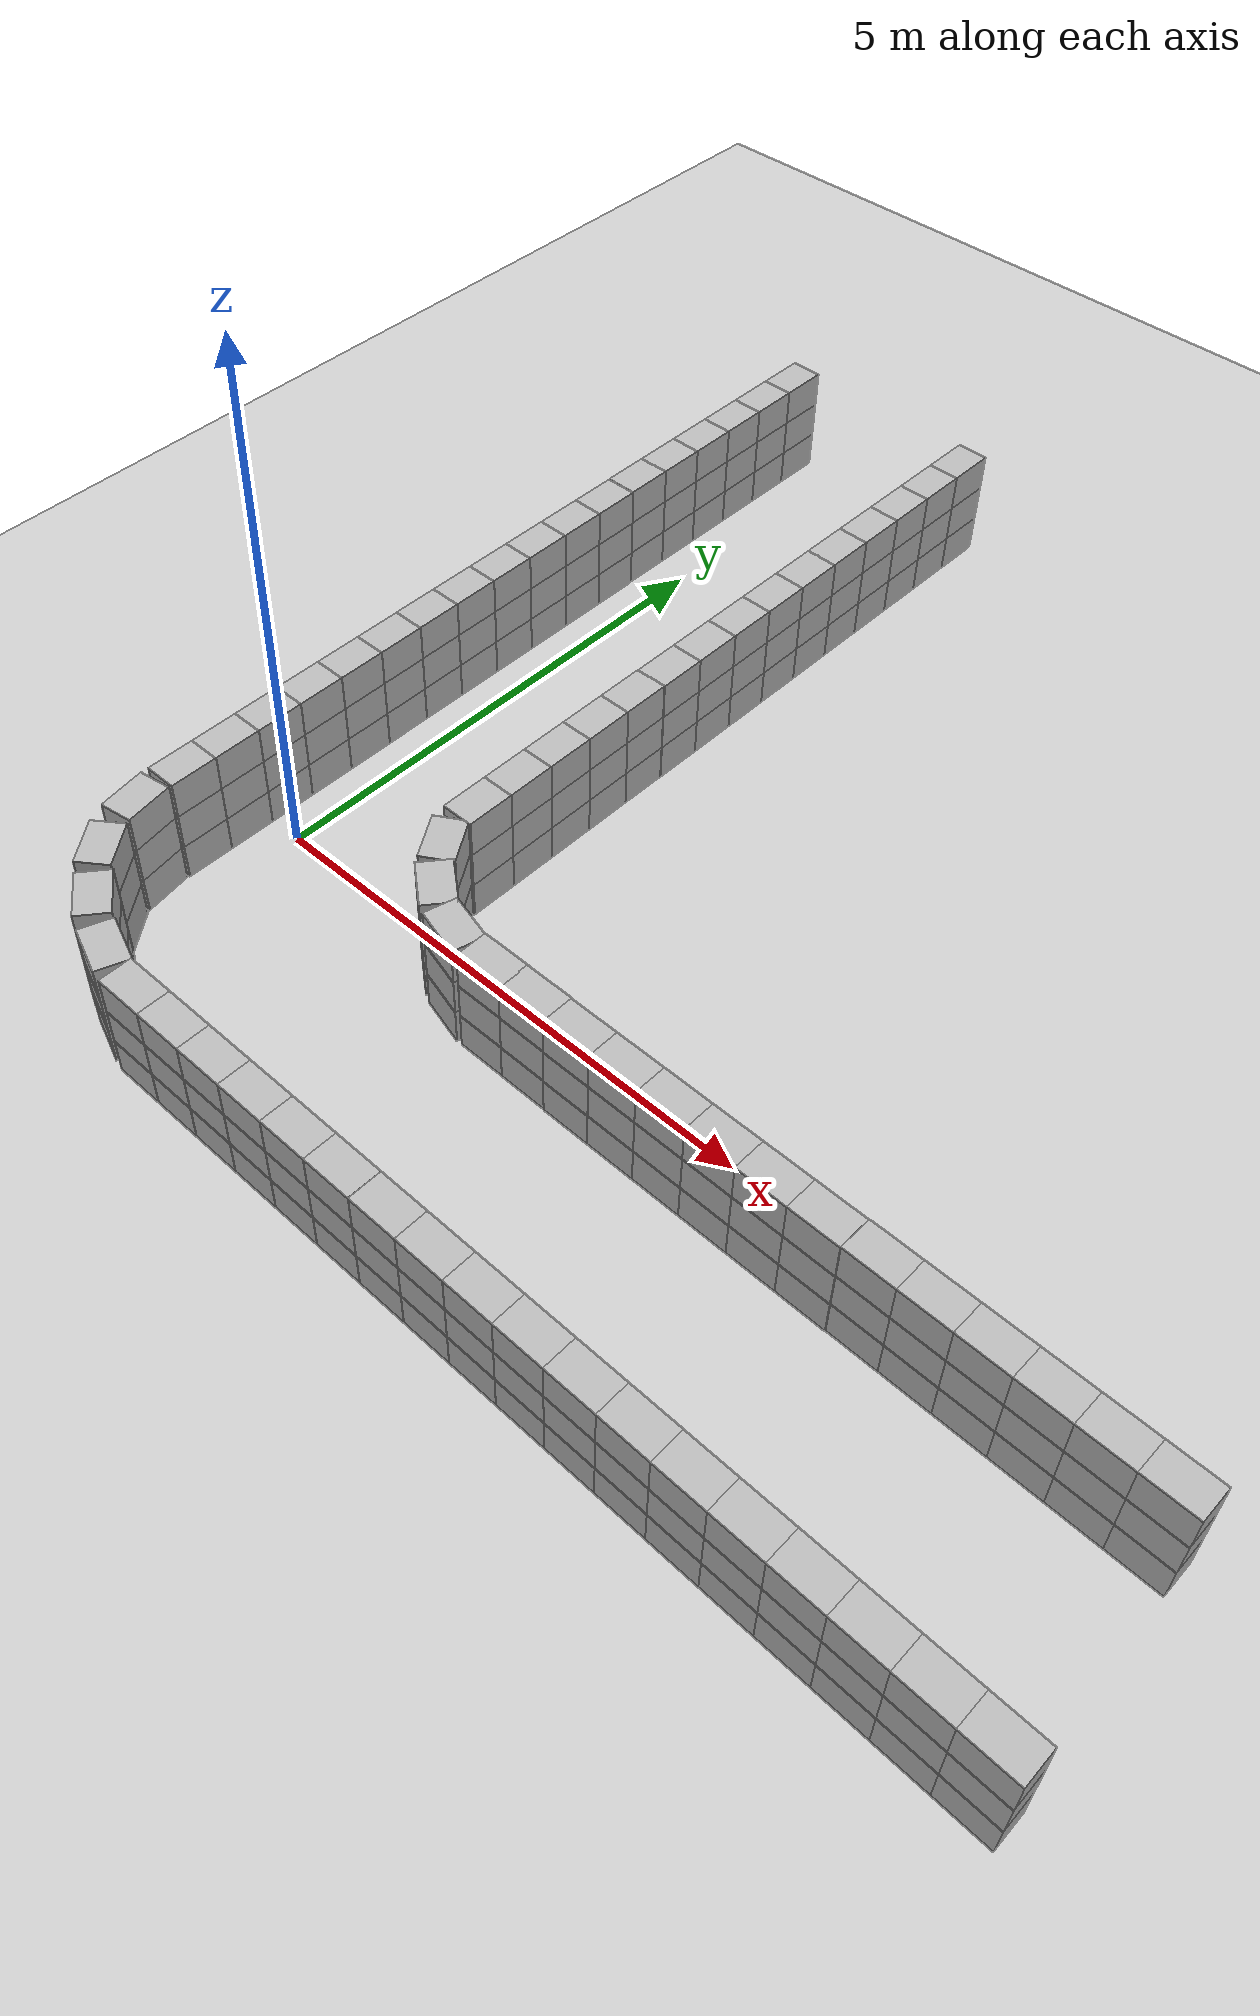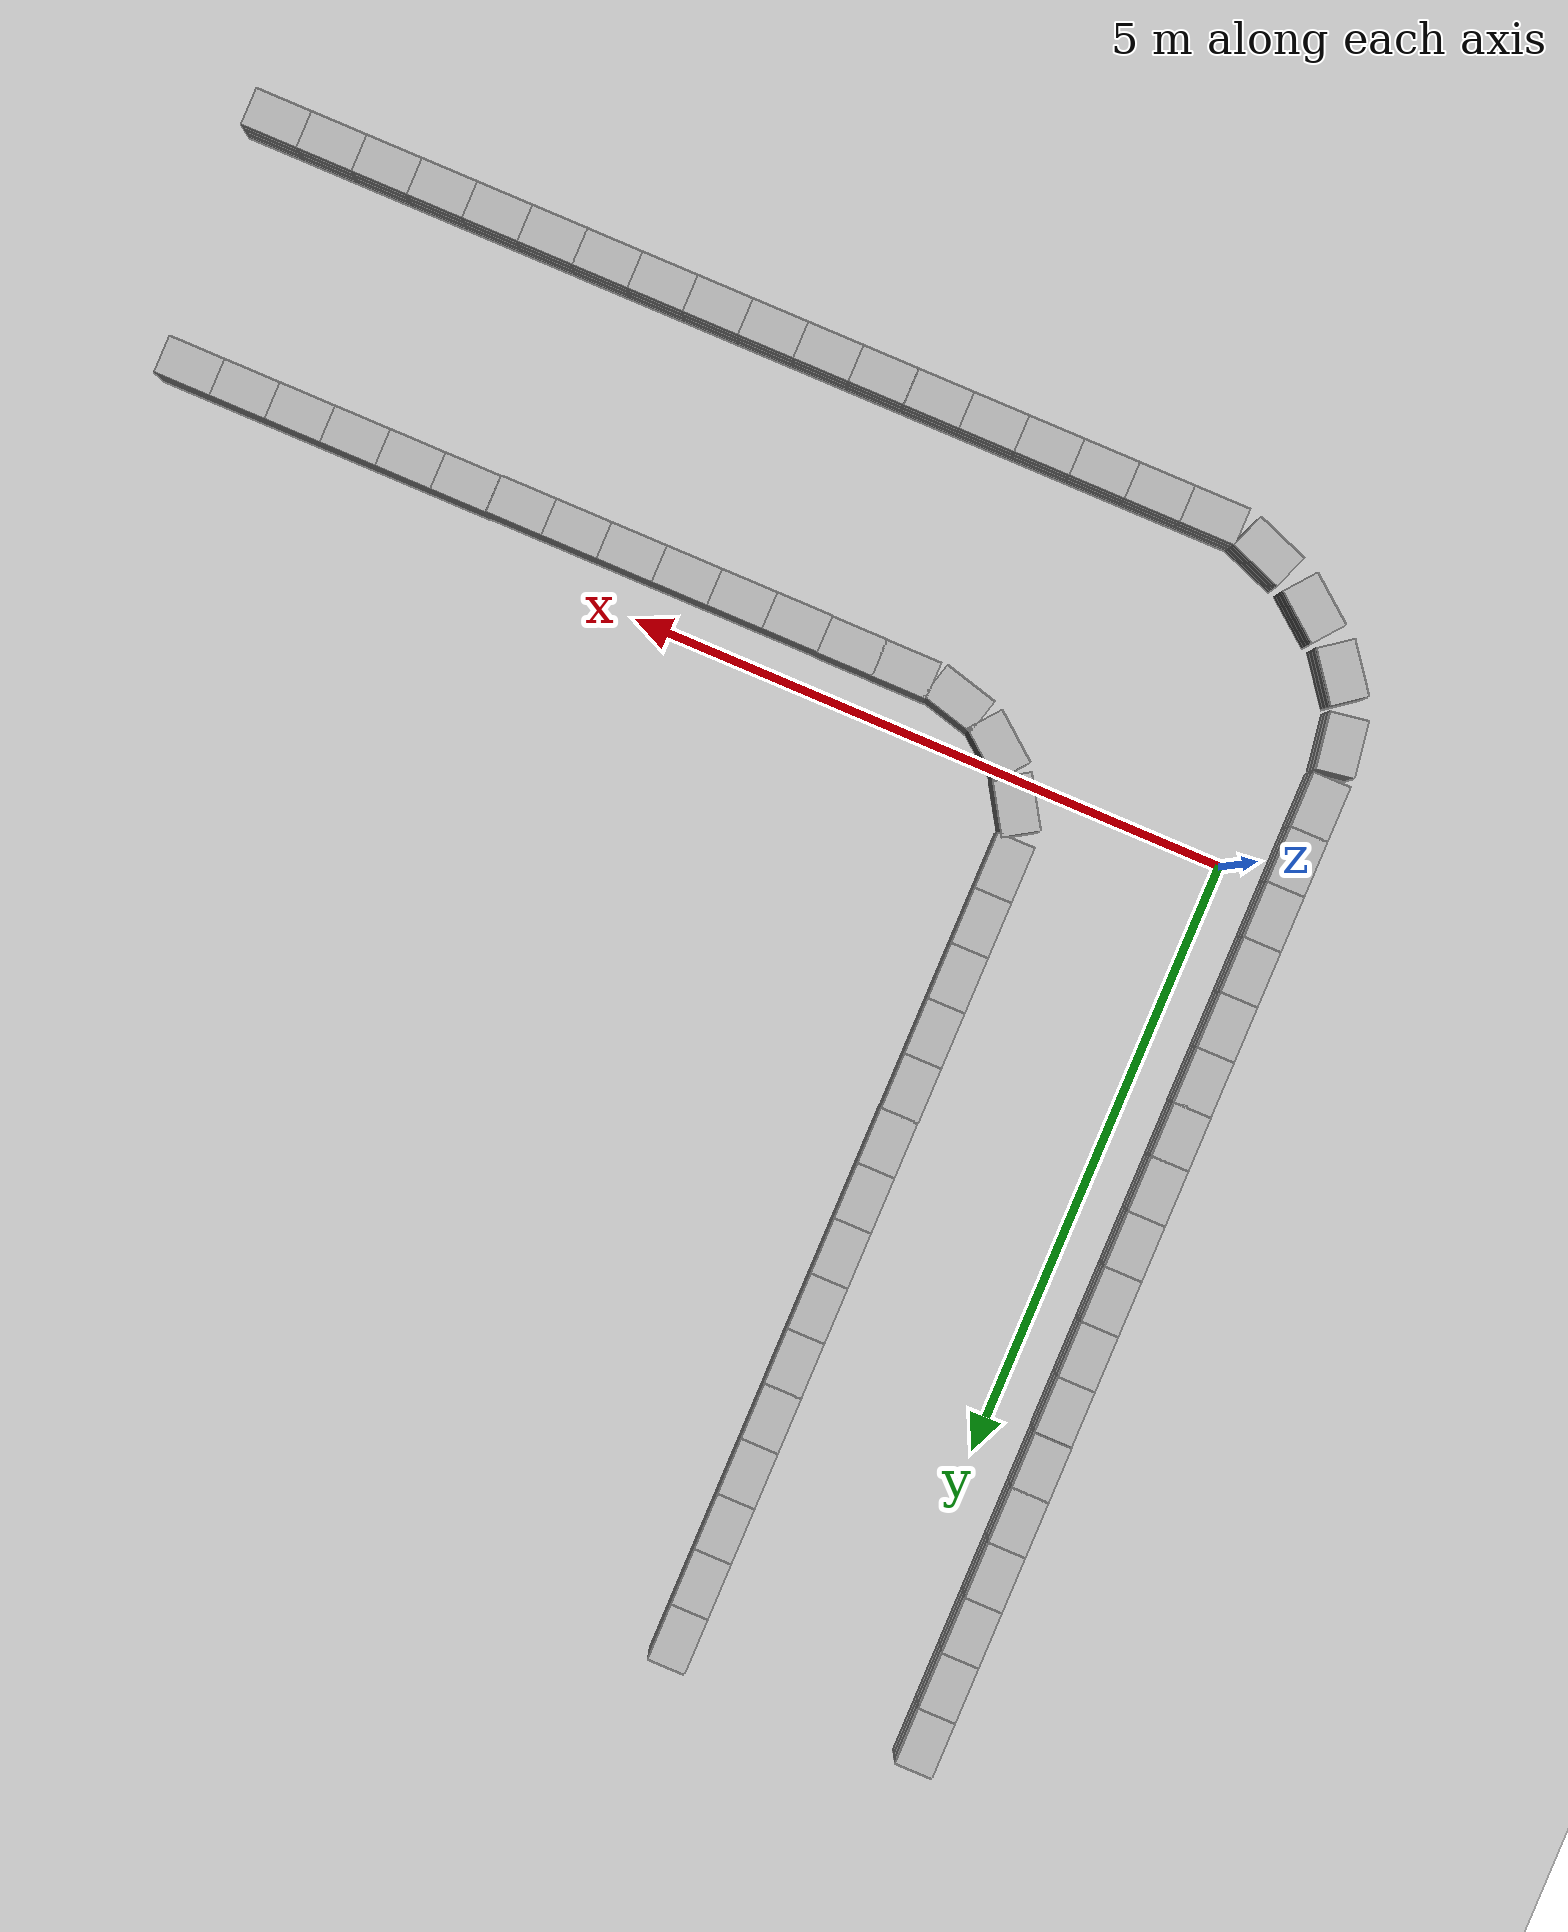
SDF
<sdf version="1.6">
 <world name="default">
  <light name="sun" type="directional">
   <pose>0 0 10 0 -0 0</pose>
   <diffuse>0.8 0.8 0.8 1</diffuse>
   <specular>0.2 0.2 0.2 1</specular>
   <attenuation>
    <range>1000</range>
    <constant>0.9</constant>
    <linear>0.01</linear>
    <quadratic>0.001</quadratic>
   </attenuation>
   <direction>-0.5 0.1 -0.9</direction>
  </light>
  <model name="ground_plane">
   <static>1</static>
   <link name="link">
    <collision name="collision">
     <geometry><plane><normal>0 0 1</normal><size>100 100</size></plane></geometry>
     <surface>
      <contact><collide_bitmask>65535</collide_bitmask></contact>
      <friction><ode><mu>100</mu><mu2>50</mu2></ode></friction>
     </surface>
    </collision>
    <visual name="visual">
     <cast_shadows>0</cast_shadows>
     <geometry><plane><normal>0 0 1</normal><size>100 100</size></plane></geometry>
     <material>
      <script><uri>file://media/materials/scripts/gazebo.material</uri><name>Gazebo/Grey</name></script>
     </material>
    </visual>
   </link>
  </model>
  <gravity>0 0 -9.8</gravity>
  <magnetic_field>6e-06 2.3e-05 -4.2e-05</magnetic_field>
  <atmosphere type="adiabatic"/>
  <physics name="default_physics" default="0" type="ode">
   <max_step_size>0.001</max_step_size>
   <real_time_factor>1</real_time_factor>
   <real_time_update_rate>1000</real_time_update_rate>
  </physics>
  <scene><ambient>0.4 0.4 0.4 1</ambient><background>0.7 0.7 0.7 1</background><shadows>1</shadows></scene>
  <audio><device>default</device></audio>
  <spherical_coordinates>
   <surface_model>EARTH_WGS84</surface_model>
   <latitude_deg>0</latitude_deg>
   <longitude_deg>0</longitude_deg>
   <elevation>0</elevation>
   <heading_deg>0</heading_deg>
  </spherical_coordinates>
  <model name="1_stack">
   <pose>0.654177 -2.37246 0 0 0 -1.93288</pose>
   <static>1</static>
   <link name="link_0">
    <collision name="collision_0">
     <pose>0 0 0.18 0 -0 3.14</pose>
     <geometry><box><size>0.31 0.465 0.36</size></box></geometry>
    </collision>
    <visual name="visual_0">
     <pose>0 0 0.18 0 -0 3.14</pose>
     <geometry><mesh><uri>model://L-corridor_curve_real/meshes/exact_blue_circle_border.dae</uri></mesh></geometry>
    </visual>
   </link>
   <link name="link_1">
    <collision name="collision_1">
     <pose>0 0 0.54 0 -0 3.14</pose>
     <geometry><box><size>0.31 0.465 0.36</size></box></geometry>
    </collision>
    <visual name="visual_1">
     <pose>0 0 0.54 0 -0 3.14</pose>
     <geometry><mesh><uri>model://L-corridor_curve_real/meshes/exact_red_circle_border.dae</uri></mesh></geometry>
    </visual>
   </link>
   <link name="link_2">
    <collision name="collision_2">
     <pose>0 0 0.9 0 -0 3.14</pose>
     <geometry><box><size>0.31 0.465 0.36</size></box></geometry>
    </collision>
    <visual name="visual_2">
     <pose>0 0 0.9 0 -0 3.14</pose>
     <geometry>
      <mesh><uri>model://L-corridor_curve_real/meshes/exact_green_circle_border.dae</uri></mesh>
     </geometry>
    </visual>
   </link>
  </model>
  <model name="1_stack_0">
   <pose>0.159717 -2.10664 0.001177 0 0 -2.24214</pose>
   <static>1</static>
   <link name="link_0">
    <collision name="collision_0">
     <pose>0 0 0.18 0 -0 3.14</pose>
     <geometry><box><size>0.31 0.465 0.36</size></box></geometry>
    </collision>
    <visual name="visual_0">
     <pose>0 0 0.18 0 -0 3.14</pose>
     <geometry><mesh><uri>model://L-corridor_curve_real/meshes/exact_blue_circle_border.dae</uri></mesh></geometry>
    </visual>
   </link>
   <link name="link_1">
    <collision name="collision_1">
     <pose>0 0 0.54 0 -0 3.14</pose>
     <geometry><box><size>0.31 0.465 0.36</size></box></geometry>
    </collision>
    <visual name="visual_1">
     <pose>0 0 0.54 0 -0 3.14</pose>
     <geometry><mesh><uri>model://L-corridor_curve_real/meshes/exact_red_circle_border.dae</uri></mesh></geometry>
    </visual>
   </link>
   <link name="link_2">
    <collision name="collision_2">
     <pose>0 0 0.9 0 -0 3.14</pose>
     <geometry><box><size>0.31 0.465 0.36</size></box></geometry>
    </collision>
    <visual name="visual_2">
     <pose>0 0 0.9 0 -0 3.14</pose>
     <geometry>
      <mesh><uri>model://L-corridor_curve_real/meshes/exact_green_circle_border.dae</uri></mesh>
     </geometry>
    </visual>
   </link>
  </model>
  <model name="1_stack_1">
   <pose>-0.453727 -1.21476 0 0 0 -2.98576</pose>
   <static>1</static>
   <link name="link_0">
    <collision name="collision_0">
     <pose>0 0 0.18 0 -0 3.14</pose>
     <geometry><box><size>0.31 0.465 0.36</size></box></geometry>
    </collision>
    <visual name="visual_0">
     <pose>0 0 0.18 0 -0 3.14</pose>
     <geometry><mesh><uri>model://L-corridor_curve_real/meshes/exact_blue_circle_border.dae</uri></mesh></geometry>
    </visual>
   </link>
   <link name="link_1">
    <collision name="collision_1">
     <pose>0 0 0.54 0 -0 3.14</pose>
     <geometry><box><size>0.31 0.465 0.36</size></box></geometry>
    </collision>
    <visual name="visual_1">
     <pose>0 0 0.54 0 -0 3.14</pose>
     <geometry><mesh><uri>model://L-corridor_curve_real/meshes/exact_red_circle_border.dae</uri></mesh></geometry>
    </visual>
   </link>
   <link name="link_2">
    <collision name="collision_2">
     <pose>0 0 0.9 0 -0 3.14</pose>
     <geometry><box><size>0.31 0.465 0.36</size></box></geometry>
    </collision>
    <visual name="visual_2">
     <pose>0 0 0.9 0 -0 3.14</pose>
     <geometry>
      <mesh><uri>model://L-corridor_curve_real/meshes/exact_green_circle_border.dae</uri></mesh>
     </geometry>
    </visual>
   </link>
  </model>
  <model name="1_stack_2">
   <pose>-0.236038 -1.73275 0 0 0 -2.4998</pose>
   <static>1</static>
   <link name="link_0">
    <collision name="collision_0">
     <pose>0 0 0.18 0 -0 3.14</pose>
     <geometry><box><size>0.31 0.465 0.36</size></box></geometry>
    </collision>
    <visual name="visual_0">
     <pose>0 0 0.18 0 -0 3.14</pose>
     <geometry><mesh><uri>model://L-corridor_curve_real/meshes/exact_blue_circle_border.dae</uri></mesh></geometry>
    </visual>
   </link>
   <link name="link_1">
    <collision name="collision_1">
     <pose>0 0 0.54 0 -0 3.14</pose>
     <geometry><box><size>0.31 0.465 0.36</size></box></geometry>
    </collision>
    <visual name="visual_1">
     <pose>0 0 0.54 0 -0 3.14</pose>
     <geometry><mesh><uri>model://L-corridor_curve_real/meshes/exact_red_circle_border.dae</uri></mesh></geometry>
    </visual>
   </link>
   <link name="link_2">
    <collision name="collision_2">
     <pose>0 0 0.9 0 -0 3.14</pose>
     <geometry><box><size>0.31 0.465 0.36</size></box></geometry>
    </collision>
    <visual name="visual_2">
     <pose>0 0 0.9 0 -0 3.14</pose>
     <geometry>
      <mesh><uri>model://L-corridor_curve_real/meshes/exact_green_circle_border.dae</uri></mesh>
     </geometry>
    </visual>
   </link>
  </model>
  <model name="realistic_curve_side1_1">
   <pose>6.13372 -0.444168 0 0 -0 1.5708</pose>
   <static>1</static>
   <link name="link_0">
    <collision name="collision_0">
     <pose>0 0 0.18 0 -0 3.14</pose>
     <geometry><box><size>0.31 0.465 0.36</size></box></geometry>
    </collision>
    <visual name="visual_0">
     <pose>0 0 0.18 0 -0 3.14</pose>
     <geometry><mesh><uri>model://L-corridor_curve_real/meshes/exact_blue_circle_border.dae</uri></mesh></geometry>
    </visual>
   </link>
   <link name="link_1">
    <collision name="collision_1">
     <pose>0 0 0.54 0 -0 3.14</pose>
     <geometry><box><size>0.31 0.465 0.36</size></box></geometry>
    </collision>
    <visual name="visual_1">
     <pose>0 0 0.54 0 -0 3.14</pose>
     <geometry><mesh><uri>model://L-corridor_curve_real/meshes/exact_red_circle_border.dae</uri></mesh></geometry>
    </visual>
   </link>
   <link name="link_2">
    <collision name="collision_2">
     <pose>0 0 0.9 0 -0 3.14</pose>
     <geometry><box><size>0.31 0.465 0.36</size></box></geometry>
    </collision>
    <visual name="visual_2">
     <pose>0 0 0.9 0 -0 3.14</pose>
     <geometry>
      <mesh><uri>model://L-corridor_curve_real/meshes/exact_green_circle_border.dae</uri></mesh>
     </geometry>
    </visual>
   </link>
   <link name="link_3">
    <collision name="collision_3">
     <pose>0 0.465 0.54 0 -0 3.14</pose>
     <geometry><box><size>0.31 0.465 0.36</size></box></geometry>
    </collision>
    <visual name="visual_3">
     <pose>0 0.465 0.54 0 -0 3.14</pose>
     <geometry><mesh><uri>model://L-corridor_curve_real/meshes/exact_blue_circle_border.dae</uri></mesh></geometry>
    </visual>
   </link>
   <link name="link_4">
    <collision name="collision_4">
     <pose>0 0.465 0.9 0 -0 3.14</pose>
     <geometry><box><size>0.31 0.465 0.36</size></box></geometry>
    </collision>
    <visual name="visual_4">
     <pose>0 0.465 0.9 0 -0 3.14</pose>
     <geometry><mesh><uri>model://L-corridor_curve_real/meshes/exact_red_circle_border.dae</uri></mesh></geometry>
    </visual>
   </link>
   <link name="link_5">
    <collision name="collision_5">
     <pose>0 0.465 0.18 0 -0 3.14</pose>
     <geometry><box><size>0.31 0.465 0.36</size></box></geometry>
    </collision>
    <visual name="visual_5">
     <pose>0 0.465 0.18 0 -0 3.14</pose>
     <geometry>
      <mesh><uri>model://L-corridor_curve_real/meshes/exact_green_circle_border.dae</uri></mesh>
     </geometry>
    </visual>
   </link>
   <link name="link_6">
    <collision name="collision_6">
     <pose>0 0.93 0.9 0 -0 3.14</pose>
     <geometry><box><size>0.31 0.465 0.36</size></box></geometry>
    </collision>
    <visual name="visual_6">
     <pose>0 0.93 0.9 0 -0 3.14</pose>
     <geometry><mesh><uri>model://L-corridor_curve_real/meshes/exact_blue_circle_border.dae</uri></mesh></geometry>
    </visual>
   </link>
   <link name="link_7">
    <collision name="collision_7">
     <pose>0 0.93 0.18 0 -0 3.14</pose>
     <geometry><box><size>0.31 0.465 0.36</size></box></geometry>
    </collision>
    <visual name="visual_7">
     <pose>0 0.93 0.18 0 -0 3.14</pose>
     <geometry><mesh><uri>model://L-corridor_curve_real/meshes/exact_red_circle_border.dae</uri></mesh></geometry>
    </visual>
   </link>
   <link name="link_8">
    <collision name="collision_8">
     <pose>0 0.93 0.54 0 -0 3.14</pose>
     <geometry><box><size>0.31 0.465 0.36</size></box></geometry>
    </collision>
    <visual name="visual_8">
     <pose>0 0.93 0.54 0 -0 3.14</pose>
     <geometry>
      <mesh><uri>model://L-corridor_curve_real/meshes/exact_green_circle_border.dae</uri></mesh>
     </geometry>
    </visual>
   </link>
   <link name="link_9">
    <collision name="collision_9">
     <pose>0 1.395 0.18 0 -0 3.14</pose>
     <geometry><box><size>0.31 0.465 0.36</size></box></geometry>
    </collision>
    <visual name="visual_9">
     <pose>0 1.395 0.18 0 -0 3.14</pose>
     <geometry><mesh><uri>model://L-corridor_curve_real/meshes/exact_blue_circle_border.dae</uri></mesh></geometry>
    </visual>
   </link>
   <link name="link_10">
    <collision name="collision_10">
     <pose>0 1.395 0.54 0 -0 3.14</pose>
     <geometry><box><size>0.31 0.465 0.36</size></box></geometry>
    </collision>
    <visual name="visual_10">
     <pose>0 1.395 0.54 0 -0 3.14</pose>
     <geometry><mesh><uri>model://L-corridor_curve_real/meshes/exact_red_circle_border.dae</uri></mesh></geometry>
    </visual>
   </link>
   <link name="link_11">
    <collision name="collision_11">
     <pose>0 1.395 0.9 0 -0 3.14</pose>
     <geometry><box><size>0.31 0.465 0.36</size></box></geometry>
    </collision>
    <visual name="visual_11">
     <pose>0 1.395 0.9 0 -0 3.14</pose>
     <geometry>
      <mesh><uri>model://L-corridor_curve_real/meshes/exact_green_circle_border.dae</uri></mesh>
     </geometry>
    </visual>
   </link>
   <link name="link_12">
    <collision name="collision_12">
     <pose>0 1.86 0.54 0 -0 3.14</pose>
     <geometry><box><size>0.31 0.465 0.36</size></box></geometry>
    </collision>
    <visual name="visual_12">
     <pose>0 1.86 0.54 0 -0 3.14</pose>
     <geometry><mesh><uri>model://L-corridor_curve_real/meshes/exact_blue_circle_border.dae</uri></mesh></geometry>
    </visual>
   </link>
   <link name="link_13">
    <collision name="collision_13">
     <pose>0 1.86 0.9 0 -0 3.14</pose>
     <geometry><box><size>0.31 0.465 0.36</size></box></geometry>
    </collision>
    <visual name="visual_13">
     <pose>0 1.86 0.9 0 -0 3.14</pose>
     <geometry><mesh><uri>model://L-corridor_curve_real/meshes/exact_red_circle_border.dae</uri></mesh></geometry>
    </visual>
   </link>
   <link name="link_14">
    <collision name="collision_14">
     <pose>0 1.86 0.18 0 -0 3.14</pose>
     <geometry><box><size>0.31 0.465 0.36</size></box></geometry>
    </collision>
    <visual name="visual_14">
     <pose>0 1.86 0.18 0 -0 3.14</pose>
     <geometry>
      <mesh><uri>model://L-corridor_curve_real/meshes/exact_green_circle_border.dae</uri></mesh>
     </geometry>
    </visual>
   </link>
   <link name="link_15">
    <collision name="collision_15">
     <pose>0 2.325 0 3.14159 0.001593 3.14159</pose>
     <geometry><box><size>0.31 0.465 0.36</size></box></geometry>
    </collision>
    <visual name="visual_15">
     <pose>0 2.325 0.9 0 -0 3.14</pose>
     <geometry><mesh><uri>model://L-corridor_curve_real/meshes/exact_blue_circle_border.dae</uri></mesh></geometry>
    </visual>
   </link>
   <link name="link_16">
    <collision name="collision_16">
     <pose>0 2.325 0.18 0 -0 3.14</pose>
     <geometry><box><size>0.31 0.465 0.36</size></box></geometry>
    </collision>
    <visual name="visual_16">
     <pose>0 2.325 0.18 0 -0 3.14</pose>
     <geometry><mesh><uri>model://L-corridor_curve_real/meshes/exact_red_circle_border.dae</uri></mesh></geometry>
    </visual>
   </link>
   <link name="link_17">
    <collision name="collision_17">
     <pose>0 2.325 0.54 0 -0 3.14</pose>
     <geometry><box><size>0.31 0.465 0.36</size></box></geometry>
    </collision>
    <visual name="visual_17">
     <pose>0 2.325 0.54 0 -0 3.14</pose>
     <geometry>
      <mesh><uri>model://L-corridor_curve_real/meshes/exact_green_circle_border.dae</uri></mesh>
     </geometry>
    </visual>
   </link>
  </model>
  <model name="realistic_curve_side2_2">
   <pose>3.96434 -1.14657 0 0 -0 1.5708</pose>
   <static>1</static>
   <link name="link_18_0">
    <collision name="collision_18_0">
     <pose>0.9 4.45 0.9 3.14159 -1.57079 3.14159</pose>
     <geometry><box><size>0.31 0.465 0.36</size></box></geometry>
    </collision>
    <visual name="visual_18_0">
     <pose>0.9 4.45 0.9 0 0 -1.5708</pose>
     <geometry><mesh><uri>model://L-corridor_curve_real/meshes/exact_blue_circle_border.dae</uri></mesh></geometry>
    </visual>
   </link>
   <link name="link_19_0">
    <collision name="collision_19_0">
     <pose>0.9 4.45 0.18 0 0 -1.5708</pose>
     <geometry><box><size>0.31 0.465 0.36</size></box></geometry>
    </collision>
    <visual name="visual_19_0">
     <pose>0.9 4.45 0.18 0 0 -1.5708</pose>
     <geometry><mesh><uri>model://L-corridor_curve_real/meshes/exact_red_circle_border.dae</uri></mesh></geometry>
    </visual>
   </link>
   <link name="link_20_0">
    <collision name="collision_20_0">
     <pose>0.9 4.45 0.54 0 0 -1.5708</pose>
     <geometry><box><size>0.31 0.465 0.36</size></box></geometry>
    </collision>
    <visual name="visual_20_0">
     <pose>0.9 4.45 0.54 0 0 -1.5708</pose>
     <geometry>
      <mesh><uri>model://L-corridor_curve_real/meshes/exact_green_circle_border.dae</uri></mesh>
     </geometry>
    </visual>
   </link>
   <link name="link_21_0">
    <collision name="collision_21_0">
     <pose>1.365 4.45 0.18 0 0 -1.5708</pose>
     <geometry><box><size>0.31 0.465 0.36</size></box></geometry>
    </collision>
    <visual name="visual_21_0">
     <pose>1.365 4.45 0.18 0 0 -1.5708</pose>
     <geometry><mesh><uri>model://L-corridor_curve_real/meshes/exact_blue_circle_border.dae</uri></mesh></geometry>
    </visual>
   </link>
   <link name="link_22_0">
    <collision name="collision_22_0">
     <pose>1.365 4.45 0.54 0 0 -1.5708</pose>
     <geometry><box><size>0.31 0.465 0.36</size></box></geometry>
    </collision>
    <visual name="visual_22_0">
     <pose>1.365 4.45 0.54 0 0 -1.5708</pose>
     <geometry><mesh><uri>model://L-corridor_curve_real/meshes/exact_red_circle_border.dae</uri></mesh></geometry>
    </visual>
   </link>
   <link name="link_23_0">
    <collision name="collision_23_0">
     <pose>1.365 4.45 0.9 0 0 -1.5708</pose>
     <geometry><box><size>0.31 0.465 0.36</size></box></geometry>
    </collision>
    <visual name="visual_23_0">
     <pose>1.365 4.45 0.9 0 0 -1.5708</pose>
     <geometry>
      <mesh><uri>model://L-corridor_curve_real/meshes/exact_green_circle_border.dae</uri></mesh>
     </geometry>
    </visual>
   </link>
   <link name="link_24_0">
    <collision name="collision_24_0">
     <pose>1.83 4.45 0.54 0 0 -1.5708</pose>
     <geometry><box><size>0.31 0.465 0.36</size></box></geometry>
    </collision>
    <visual name="visual_24_0">
     <pose>1.83 4.45 0.54 0 0 -1.5708</pose>
     <geometry><mesh><uri>model://L-corridor_curve_real/meshes/exact_blue_circle_border.dae</uri></mesh></geometry>
    </visual>
   </link>
   <link name="link_25_0">
    <collision name="collision_25_0">
     <pose>1.83 4.45 0.9 0 0 -1.5708</pose>
     <geometry><box><size>0.31 0.465 0.36</size></box></geometry>
    </collision>
    <visual name="visual_25_0">
     <pose>1.83 4.45 0.9 0 0 -1.5708</pose>
     <geometry><mesh><uri>model://L-corridor_curve_real/meshes/exact_red_circle_border.dae</uri></mesh></geometry>
    </visual>
   </link>
   <link name="link_26_0">
    <collision name="collision_26_0">
     <pose>1.83 4.45 0.18 0 0 -1.5708</pose>
     <geometry><box><size>0.31 0.465 0.36</size></box></geometry>
    </collision>
    <visual name="visual_26_0">
     <pose>1.83 4.45 0.18 0 0 -1.5708</pose>
     <geometry>
      <mesh><uri>model://L-corridor_curve_real/meshes/exact_green_circle_border.dae</uri></mesh>
     </geometry>
    </visual>
   </link>
   <link name="link_27_0">
    <collision name="collision_27_0">
     <pose>2.295 4.45 0.9 3.14159 -1.57079 3.14159</pose>
     <geometry><box><size>0.31 0.465 0.36</size></box></geometry>
    </collision>
    <visual name="visual_27_0">
     <pose>2.295 4.45 0.9 0 0 -1.5708</pose>
     <geometry><mesh><uri>model://L-corridor_curve_real/meshes/exact_blue_circle_border.dae</uri></mesh></geometry>
    </visual>
   </link>
   <link name="link_28_0">
    <collision name="collision_28_0">
     <pose>2.295 4.45 0.18 0 0 -1.5708</pose>
     <geometry><box><size>0.31 0.465 0.36</size></box></geometry>
    </collision>
    <visual name="visual_28_0">
     <pose>2.295 4.45 0.18 0 0 -1.5708</pose>
     <geometry><mesh><uri>model://L-corridor_curve_real/meshes/exact_red_circle_border.dae</uri></mesh></geometry>
    </visual>
   </link>
   <link name="link_29_0">
    <collision name="collision_29_0">
     <pose>2.295 4.45 0.54 0 0 -1.5708</pose>
     <geometry><box><size>0.31 0.465 0.36</size></box></geometry>
    </collision>
    <visual name="visual_29_0">
     <pose>2.295 4.45 0.54 0 0 -1.5708</pose>
     <geometry>
      <mesh><uri>model://L-corridor_curve_real/meshes/exact_green_circle_border.dae</uri></mesh>
     </geometry>
    </visual>
   </link>
   <link name="link_30_0">
    <collision name="collision_30_0">
     <pose>2.76 4.45 0.18 0 0 -1.5708</pose>
     <geometry><box><size>0.31 0.465 0.36</size></box></geometry>
    </collision>
    <visual name="visual_30_0">
     <pose>2.76 4.45 0.18 0 0 -1.5708</pose>
     <geometry><mesh><uri>model://L-corridor_curve_real/meshes/exact_blue_circle_border.dae</uri></mesh></geometry>
    </visual>
   </link>
   <link name="link_31_0">
    <collision name="collision_31_0">
     <pose>2.76 4.45 0.54 0 0 -1.5708</pose>
     <geometry><box><size>0.31 0.465 0.36</size></box></geometry>
    </collision>
    <visual name="visual_31_0">
     <pose>2.76 4.45 0.54 0 0 -1.5708</pose>
     <geometry><mesh><uri>model://L-corridor_curve_real/meshes/exact_red_circle_border.dae</uri></mesh></geometry>
    </visual>
   </link>
   <link name="link_32_0">
    <collision name="collision_32_0">
     <pose>2.76 4.45 0.9 0 0 -1.5708</pose>
     <geometry><box><size>0.31 0.465 0.36</size></box></geometry>
    </collision>
    <visual name="visual_32_0">
     <pose>2.76 4.45 0.9 0 0 -1.5708</pose>
     <geometry>
      <mesh><uri>model://L-corridor_curve_real/meshes/exact_green_circle_border.dae</uri></mesh>
     </geometry>
    </visual>
   </link>
   <link name="link_33_0">
    <collision name="collision_33_0">
     <pose>0.44 4.45 0.54 0 0 -1.5708</pose>
     <geometry><box><size>0.31 0.465 0.36</size></box></geometry>
    </collision>
    <visual name="visual_33_0">
     <pose>0.44 4.45 0.54 0 0 -1.5708</pose>
     <geometry><mesh><uri>model://L-corridor_curve_real/meshes/exact_blue_circle_border.dae</uri></mesh></geometry>
    </visual>
   </link>
   <link name="link_34_0">
    <collision name="collision_34_0">
     <pose>0.4 4.45 0.9 0 0 -1.5708</pose>
     <geometry><box><size>0.31 0.465 0.36</size></box></geometry>
    </collision>
    <visual name="visual_34_0">
     <pose>0.44 4.45 0.9 0 0 -1.5708</pose>
     <geometry><mesh><uri>model://L-corridor_curve_real/meshes/exact_red_circle_border.dae</uri></mesh></geometry>
    </visual>
   </link>
   <link name="link_35_0">
    <collision name="collision_35_0">
     <pose>0.44 4.45 0.18 0 0 -1.5708</pose>
     <geometry><box><size>0.31 0.465 0.36</size></box></geometry>
    </collision>
    <visual name="visual_35_0">
     <pose>0.44 4.45 0.18 0 0 -1.5708</pose>
     <geometry>
      <mesh><uri>model://L-corridor_curve_real/meshes/exact_green_circle_border.dae</uri></mesh>
     </geometry>
    </visual>
   </link>
  </model>
  <model name="realistic_curve_side2_2_0">
   <pose>3.96188 1.62711 0 0 -0 1.5708</pose>
   <static>1</static>
   <link name="link_18_0">
    <collision name="collision_18_0">
     <pose>0.9 4.45 0.9 3.14159 -1.57079 3.14159</pose>
     <geometry><box><size>0.31 0.465 0.36</size></box></geometry>
    </collision>
    <visual name="visual_18_0">
     <pose>0.9 4.45 0.9 0 0 -1.5708</pose>
     <geometry><mesh><uri>model://L-corridor_curve_real/meshes/exact_blue_circle_border.dae</uri></mesh></geometry>
    </visual>
   </link>
   <link name="link_19_0">
    <collision name="collision_19_0">
     <pose>0.9 4.45 0.18 0 0 -1.5708</pose>
     <geometry><box><size>0.31 0.465 0.36</size></box></geometry>
    </collision>
    <visual name="visual_19_0">
     <pose>0.9 4.45 0.18 0 0 -1.5708</pose>
     <geometry><mesh><uri>model://L-corridor_curve_real/meshes/exact_red_circle_border.dae</uri></mesh></geometry>
    </visual>
   </link>
   <link name="link_20_0">
    <collision name="collision_20_0">
     <pose>0.9 4.45 0.54 0 0 -1.5708</pose>
     <geometry><box><size>0.31 0.465 0.36</size></box></geometry>
    </collision>
    <visual name="visual_20_0">
     <pose>0.9 4.45 0.54 0 0 -1.5708</pose>
     <geometry>
      <mesh><uri>model://L-corridor_curve_real/meshes/exact_green_circle_border.dae</uri></mesh>
     </geometry>
    </visual>
   </link>
   <link name="link_21_0">
    <collision name="collision_21_0">
     <pose>1.365 4.45 0.18 0 0 -1.5708</pose>
     <geometry><box><size>0.31 0.465 0.36</size></box></geometry>
    </collision>
    <visual name="visual_21_0">
     <pose>1.365 4.45 0.18 0 0 -1.5708</pose>
     <geometry><mesh><uri>model://L-corridor_curve_real/meshes/exact_blue_circle_border.dae</uri></mesh></geometry>
    </visual>
   </link>
   <link name="link_22_0">
    <collision name="collision_22_0">
     <pose>1.365 4.45 0.54 0 0 -1.5708</pose>
     <geometry><box><size>0.31 0.465 0.36</size></box></geometry>
    </collision>
    <visual name="visual_22_0">
     <pose>1.365 4.45 0.54 0 0 -1.5708</pose>
     <geometry><mesh><uri>model://L-corridor_curve_real/meshes/exact_red_circle_border.dae</uri></mesh></geometry>
    </visual>
   </link>
   <link name="link_23_0">
    <collision name="collision_23_0">
     <pose>1.365 4.45 0.9 0 0 -1.5708</pose>
     <geometry><box><size>0.31 0.465 0.36</size></box></geometry>
    </collision>
    <visual name="visual_23_0">
     <pose>1.365 4.45 0.9 0 0 -1.5708</pose>
     <geometry>
      <mesh><uri>model://L-corridor_curve_real/meshes/exact_green_circle_border.dae</uri></mesh>
     </geometry>
    </visual>
   </link>
   <link name="link_24_0">
    <collision name="collision_24_0">
     <pose>1.83 4.45 0.54 0 0 -1.5708</pose>
     <geometry><box><size>0.31 0.465 0.36</size></box></geometry>
    </collision>
    <visual name="visual_24_0">
     <pose>1.83 4.45 0.54 0 0 -1.5708</pose>
     <geometry><mesh><uri>model://L-corridor_curve_real/meshes/exact_blue_circle_border.dae</uri></mesh></geometry>
    </visual>
   </link>
   <link name="link_25_0">
    <collision name="collision_25_0">
     <pose>1.83 4.45 0.9 0 0 -1.5708</pose>
     <geometry><box><size>0.31 0.465 0.36</size></box></geometry>
    </collision>
    <visual name="visual_25_0">
     <pose>1.83 4.45 0.9 0 0 -1.5708</pose>
     <geometry><mesh><uri>model://L-corridor_curve_real/meshes/exact_red_circle_border.dae</uri></mesh></geometry>
    </visual>
   </link>
   <link name="link_26_0">
    <collision name="collision_26_0">
     <pose>1.83 4.45 0.18 0 0 -1.5708</pose>
     <geometry><box><size>0.31 0.465 0.36</size></box></geometry>
    </collision>
    <visual name="visual_26_0">
     <pose>1.83 4.45 0.18 0 0 -1.5708</pose>
     <geometry>
      <mesh><uri>model://L-corridor_curve_real/meshes/exact_green_circle_border.dae</uri></mesh>
     </geometry>
    </visual>
   </link>
   <link name="link_27_0">
    <collision name="collision_27_0">
     <pose>2.295 4.45 0.9 3.14159 -1.57079 3.14159</pose>
     <geometry><box><size>0.31 0.465 0.36</size></box></geometry>
    </collision>
    <visual name="visual_27_0">
     <pose>2.295 4.45 0.9 0 0 -1.5708</pose>
     <geometry><mesh><uri>model://L-corridor_curve_real/meshes/exact_blue_circle_border.dae</uri></mesh></geometry>
    </visual>
   </link>
   <link name="link_28_0">
    <collision name="collision_28_0">
     <pose>2.295 4.45 0.18 0 0 -1.5708</pose>
     <geometry><box><size>0.31 0.465 0.36</size></box></geometry>
    </collision>
    <visual name="visual_28_0">
     <pose>2.295 4.45 0.18 0 0 -1.5708</pose>
     <geometry><mesh><uri>model://L-corridor_curve_real/meshes/exact_red_circle_border.dae</uri></mesh></geometry>
    </visual>
   </link>
   <link name="link_29_0">
    <collision name="collision_29_0">
     <pose>2.295 4.45 0.54 0 0 -1.5708</pose>
     <geometry><box><size>0.31 0.465 0.36</size></box></geometry>
    </collision>
    <visual name="visual_29_0">
     <pose>2.295 4.45 0.54 0 0 -1.5708</pose>
     <geometry>
      <mesh><uri>model://L-corridor_curve_real/meshes/exact_green_circle_border.dae</uri></mesh>
     </geometry>
    </visual>
   </link>
   <link name="link_30_0">
    <collision name="collision_30_0">
     <pose>2.76 4.45 0.18 0 0 -1.5708</pose>
     <geometry><box><size>0.31 0.465 0.36</size></box></geometry>
    </collision>
    <visual name="visual_30_0">
     <pose>2.76 4.45 0.18 0 0 -1.5708</pose>
     <geometry><mesh><uri>model://L-corridor_curve_real/meshes/exact_blue_circle_border.dae</uri></mesh></geometry>
    </visual>
   </link>
   <link name="link_31_0">
    <collision name="collision_31_0">
     <pose>2.76 4.45 0.54 0 0 -1.5708</pose>
     <geometry><box><size>0.31 0.465 0.36</size></box></geometry>
    </collision>
    <visual name="visual_31_0">
     <pose>2.76 4.45 0.54 0 0 -1.5708</pose>
     <geometry><mesh><uri>model://L-corridor_curve_real/meshes/exact_red_circle_border.dae</uri></mesh></geometry>
    </visual>
   </link>
   <link name="link_32_0">
    <collision name="collision_32_0">
     <pose>2.76 4.45 0.9 0 0 -1.5708</pose>
     <geometry><box><size>0.31 0.465 0.36</size></box></geometry>
    </collision>
    <visual name="visual_32_0">
     <pose>2.76 4.45 0.9 0 0 -1.5708</pose>
     <geometry>
      <mesh><uri>model://L-corridor_curve_real/meshes/exact_green_circle_border.dae</uri></mesh>
     </geometry>
    </visual>
   </link>
   <link name="link_33_0">
    <collision name="collision_33_0">
     <pose>0.44 4.45 0.54 0 0 -1.5708</pose>
     <geometry><box><size>0.31 0.465 0.36</size></box></geometry>
    </collision>
    <visual name="visual_33_0">
     <pose>0.44 4.45 0.54 0 0 -1.5708</pose>
     <geometry><mesh><uri>model://L-corridor_curve_real/meshes/exact_blue_circle_border.dae</uri></mesh></geometry>
    </visual>
   </link>
   <link name="link_34_0">
    <collision name="collision_34_0">
     <pose>0.4 4.45 0.9 0 0 -1.5708</pose>
     <geometry><box><size>0.31 0.465 0.36</size></box></geometry>
    </collision>
    <visual name="visual_34_0">
     <pose>0.44 4.45 0.9 0 0 -1.5708</pose>
     <geometry><mesh><uri>model://L-corridor_curve_real/meshes/exact_red_circle_border.dae</uri></mesh></geometry>
    </visual>
   </link>
   <link name="link_35_0">
    <collision name="collision_35_0">
     <pose>0.44 4.45 0.18 0 0 -1.5708</pose>
     <geometry><box><size>0.31 0.465 0.36</size></box></geometry>
    </collision>
    <visual name="visual_35_0">
     <pose>0.44 4.45 0.18 0 0 -1.5708</pose>
     <geometry>
      <mesh><uri>model://L-corridor_curve_real/meshes/exact_green_circle_border.dae</uri></mesh>
     </geometry>
    </visual>
   </link>
  </model>
  <model name="realistic_curve_side1_1_0">
   <pose>8.92526 -0.439347 0 0 -0 1.5708</pose>
   <static>1</static>
   <link name="link_0">
    <collision name="collision_0">
     <pose>0 0 0.18 0 -0 3.14</pose>
     <geometry><box><size>0.31 0.465 0.36</size></box></geometry>
    </collision>
    <visual name="visual_0">
     <pose>0 0 0.18 0 -0 3.14</pose>
     <geometry><mesh><uri>model://L-corridor_curve_real/meshes/exact_blue_circle_border.dae</uri></mesh></geometry>
    </visual>
   </link>
   <link name="link_1">
    <collision name="collision_1">
     <pose>0 0 0.54 0 -0 3.14</pose>
     <geometry><box><size>0.31 0.465 0.36</size></box></geometry>
    </collision>
    <visual name="visual_1">
     <pose>0 0 0.54 0 -0 3.14</pose>
     <geometry><mesh><uri>model://L-corridor_curve_real/meshes/exact_red_circle_border.dae</uri></mesh></geometry>
    </visual>
   </link>
   <link name="link_2">
    <collision name="collision_2">
     <pose>0 0 0.9 0 -0 3.14</pose>
     <geometry><box><size>0.31 0.465 0.36</size></box></geometry>
    </collision>
    <visual name="visual_2">
     <pose>0 0 0.9 0 -0 3.14</pose>
     <geometry>
      <mesh><uri>model://L-corridor_curve_real/meshes/exact_green_circle_border.dae</uri></mesh>
     </geometry>
    </visual>
   </link>
   <link name="link_3">
    <collision name="collision_3">
     <pose>0 0.465 0.54 0 -0 3.14</pose>
     <geometry><box><size>0.31 0.465 0.36</size></box></geometry>
    </collision>
    <visual name="visual_3">
     <pose>0 0.465 0.54 0 -0 3.14</pose>
     <geometry><mesh><uri>model://L-corridor_curve_real/meshes/exact_blue_circle_border.dae</uri></mesh></geometry>
    </visual>
   </link>
   <link name="link_4">
    <collision name="collision_4">
     <pose>0 0.465 0.9 0 -0 3.14</pose>
     <geometry><box><size>0.31 0.465 0.36</size></box></geometry>
    </collision>
    <visual name="visual_4">
     <pose>0 0.465 0.9 0 -0 3.14</pose>
     <geometry><mesh><uri>model://L-corridor_curve_real/meshes/exact_red_circle_border.dae</uri></mesh></geometry>
    </visual>
   </link>
   <link name="link_5">
    <collision name="collision_5">
     <pose>0 0.465 0.18 0 -0 3.14</pose>
     <geometry><box><size>0.31 0.465 0.36</size></box></geometry>
    </collision>
    <visual name="visual_5">
     <pose>0 0.465 0.18 0 -0 3.14</pose>
     <geometry>
      <mesh><uri>model://L-corridor_curve_real/meshes/exact_green_circle_border.dae</uri></mesh>
     </geometry>
    </visual>
   </link>
   <link name="link_6">
    <collision name="collision_6">
     <pose>0 0.93 0.9 0 -0 3.14</pose>
     <geometry><box><size>0.31 0.465 0.36</size></box></geometry>
    </collision>
    <visual name="visual_6">
     <pose>0 0.93 0.9 0 -0 3.14</pose>
     <geometry><mesh><uri>model://L-corridor_curve_real/meshes/exact_blue_circle_border.dae</uri></mesh></geometry>
    </visual>
   </link>
   <link name="link_7">
    <collision name="collision_7">
     <pose>0 0.93 0.18 0 -0 3.14</pose>
     <geometry><box><size>0.31 0.465 0.36</size></box></geometry>
    </collision>
    <visual name="visual_7">
     <pose>0 0.93 0.18 0 -0 3.14</pose>
     <geometry><mesh><uri>model://L-corridor_curve_real/meshes/exact_red_circle_border.dae</uri></mesh></geometry>
    </visual>
   </link>
   <link name="link_8">
    <collision name="collision_8">
     <pose>0 0.93 0.54 0 -0 3.14</pose>
     <geometry><box><size>0.31 0.465 0.36</size></box></geometry>
    </collision>
    <visual name="visual_8">
     <pose>0 0.93 0.54 0 -0 3.14</pose>
     <geometry>
      <mesh><uri>model://L-corridor_curve_real/meshes/exact_green_circle_border.dae</uri></mesh>
     </geometry>
    </visual>
   </link>
   <link name="link_9">
    <collision name="collision_9">
     <pose>0 1.395 0.18 0 -0 3.14</pose>
     <geometry><box><size>0.31 0.465 0.36</size></box></geometry>
    </collision>
    <visual name="visual_9">
     <pose>0 1.395 0.18 0 -0 3.14</pose>
     <geometry><mesh><uri>model://L-corridor_curve_real/meshes/exact_blue_circle_border.dae</uri></mesh></geometry>
    </visual>
   </link>
   <link name="link_10">
    <collision name="collision_10">
     <pose>0 1.395 0.54 0 -0 3.14</pose>
     <geometry><box><size>0.31 0.465 0.36</size></box></geometry>
    </collision>
    <visual name="visual_10">
     <pose>0 1.395 0.54 0 -0 3.14</pose>
     <geometry><mesh><uri>model://L-corridor_curve_real/meshes/exact_red_circle_border.dae</uri></mesh></geometry>
    </visual>
   </link>
   <link name="link_11">
    <collision name="collision_11">
     <pose>0 1.395 0.9 0 -0 3.14</pose>
     <geometry><box><size>0.31 0.465 0.36</size></box></geometry>
    </collision>
    <visual name="visual_11">
     <pose>0 1.395 0.9 0 -0 3.14</pose>
     <geometry>
      <mesh><uri>model://L-corridor_curve_real/meshes/exact_green_circle_border.dae</uri></mesh>
     </geometry>
    </visual>
   </link>
   <link name="link_12">
    <collision name="collision_12">
     <pose>0 1.86 0.54 0 -0 3.14</pose>
     <geometry><box><size>0.31 0.465 0.36</size></box></geometry>
    </collision>
    <visual name="visual_12">
     <pose>0 1.86 0.54 0 -0 3.14</pose>
     <geometry><mesh><uri>model://L-corridor_curve_real/meshes/exact_blue_circle_border.dae</uri></mesh></geometry>
    </visual>
   </link>
   <link name="link_13">
    <collision name="collision_13">
     <pose>0 1.86 0.9 0 -0 3.14</pose>
     <geometry><box><size>0.31 0.465 0.36</size></box></geometry>
    </collision>
    <visual name="visual_13">
     <pose>0 1.86 0.9 0 -0 3.14</pose>
     <geometry><mesh><uri>model://L-corridor_curve_real/meshes/exact_red_circle_border.dae</uri></mesh></geometry>
    </visual>
   </link>
   <link name="link_14">
    <collision name="collision_14">
     <pose>0 1.86 0.18 0 -0 3.14</pose>
     <geometry><box><size>0.31 0.465 0.36</size></box></geometry>
    </collision>
    <visual name="visual_14">
     <pose>0 1.86 0.18 0 -0 3.14</pose>
     <geometry>
      <mesh><uri>model://L-corridor_curve_real/meshes/exact_green_circle_border.dae</uri></mesh>
     </geometry>
    </visual>
   </link>
   <link name="link_15">
    <collision name="collision_15">
     <pose>0 2.325 0 3.14159 0.001593 3.14159</pose>
     <geometry><box><size>0.31 0.465 0.36</size></box></geometry>
    </collision>
    <visual name="visual_15">
     <pose>0 2.325 0.9 0 -0 3.14</pose>
     <geometry><mesh><uri>model://L-corridor_curve_real/meshes/exact_blue_circle_border.dae</uri></mesh></geometry>
    </visual>
   </link>
   <link name="link_16">
    <collision name="collision_16">
     <pose>0 2.325 0.18 0 -0 3.14</pose>
     <geometry><box><size>0.31 0.465 0.36</size></box></geometry>
    </collision>
    <visual name="visual_16">
     <pose>0 2.325 0.18 0 -0 3.14</pose>
     <geometry><mesh><uri>model://L-corridor_curve_real/meshes/exact_red_circle_border.dae</uri></mesh></geometry>
    </visual>
   </link>
   <link name="link_17">
    <collision name="collision_17">
     <pose>0 2.325 0.54 0 -0 3.14</pose>
     <geometry><box><size>0.31 0.465 0.36</size></box></geometry>
    </collision>
    <visual name="visual_17">
     <pose>0 2.325 0.54 0 -0 3.14</pose>
     <geometry>
      <mesh><uri>model://L-corridor_curve_real/meshes/exact_green_circle_border.dae</uri></mesh>
     </geometry>
    </visual>
   </link>
  </model>
  <model name="realistic_curve_side2_1">
   <pose>3.4742 -1.16832 0 0 -0 1.5708</pose>
   <static>1</static>
   <link name="link_0_0">
    <collision name="collision_0_0">
     <pose>-1.3 0 0.18 0 -0 0</pose>
     <geometry><box><size>0.31 0.465 0.36</size></box></geometry>
    </collision>
    <visual name="visual_0_0">
     <pose>-1.3 0 0.18 0 -0 0</pose>
     <geometry><mesh><uri>model://L-corridor_curve_real/meshes/exact_blue_circle_border.dae</uri></mesh></geometry>
    </visual>
   </link>
   <link name="link_1_0">
    <collision name="collision_1_0">
     <pose>-1.3 0.54 0 0 -0 0</pose>
     <geometry><box><size>0.31 0.465 0.36</size></box></geometry>
    </collision>
    <visual name="visual_1_0">
     <pose>-1.3 0 0.54 0 -0 0</pose>
     <geometry><mesh><uri>model://L-corridor_curve_real/meshes/exact_red_circle_border.dae</uri></mesh></geometry>
    </visual>
   </link>
   <link name="link_2_0">
    <collision name="collision_2_0">
     <pose>-1.3 0 0.9 0 -0 0</pose>
     <geometry><box><size>0.31 0.465 0.36</size></box></geometry>
    </collision>
    <visual name="visual_2_0">
     <pose>-1.3 0 0.9 0 -0 0</pose>
     <geometry>
      <mesh><uri>model://L-corridor_curve_real/meshes/exact_green_circle_border.dae</uri></mesh>
     </geometry>
    </visual>
   </link>
   <link name="link_3_0">
    <collision name="collision_3_0">
     <pose>-1.3 0.465 0.54 0 -0 0</pose>
     <geometry><box><size>0.31 0.465 0.36</size></box></geometry>
    </collision>
    <visual name="visual_3_0">
     <pose>-1.3 0.465 0.54 0 -0 0</pose>
     <geometry><mesh><uri>model://L-corridor_curve_real/meshes/exact_blue_circle_border.dae</uri></mesh></geometry>
    </visual>
   </link>
   <link name="link_4_0">
    <collision name="collision_4_0">
     <pose>-1.3 0.465 0.9 0 -0 0</pose>
     <geometry><box><size>0.31 0.465 0.36</size></box></geometry>
    </collision>
    <visual name="visual_4_0">
     <pose>-1.3 0.465 0.9 0 -0 0</pose>
     <geometry><mesh><uri>model://L-corridor_curve_real/meshes/exact_red_circle_border.dae</uri></mesh></geometry>
    </visual>
   </link>
   <link name="link_5_0">
    <collision name="collision_5_0">
     <pose>-1.3 0.465 0.18 0 -0 0</pose>
     <geometry><box><size>0.31 0.465 0.36</size></box></geometry>
    </collision>
    <visual name="visual_5_0">
     <pose>-1.3 0.465 0.18 0 -0 0</pose>
     <geometry>
      <mesh><uri>model://L-corridor_curve_real/meshes/exact_green_circle_border.dae</uri></mesh>
     </geometry>
    </visual>
   </link>
   <link name="link_6_0">
    <collision name="collision_6_0">
     <pose>-1.3 0.93 0.9 0 -0 0</pose>
     <geometry><box><size>0.31 0.465 0.36</size></box></geometry>
    </collision>
    <visual name="visual_6_0">
     <pose>-1.3 0.93 0.9 0 -0 0</pose>
     <geometry><mesh><uri>model://L-corridor_curve_real/meshes/exact_blue_circle_border.dae</uri></mesh></geometry>
    </visual>
   </link>
   <link name="link_7_0">
    <collision name="collision_7_0">
     <pose>-1.3 0.93 0.18 0 -0 0</pose>
     <geometry><box><size>0.31 0.465 0.36</size></box></geometry>
    </collision>
    <visual name="visual_7_0">
     <pose>-1.3 0.93 0.18 0 -0 0</pose>
     <geometry><mesh><uri>model://L-corridor_curve_real/meshes/exact_red_circle_border.dae</uri></mesh></geometry>
    </visual>
   </link>
   <link name="link_8_0">
    <collision name="collision_8_0">
     <pose>-1.3 0.93 0.54 0 -0 0</pose>
     <geometry><box><size>0.31 0.465 0.36</size></box></geometry>
    </collision>
    <visual name="visual_8_0">
     <pose>-1.3 0.93 0.54 0 -0 0</pose>
     <geometry>
      <mesh><uri>model://L-corridor_curve_real/meshes/exact_green_circle_border.dae</uri></mesh>
     </geometry>
    </visual>
   </link>
   <link name="link_9_0">
    <collision name="collision_9_0">
     <pose>-1.3 1.395 0.18 0 -0 0</pose>
     <geometry><box><size>0.31 0.465 0.36</size></box></geometry>
    </collision>
    <visual name="visual_9_0">
     <pose>-1.3 1.395 0.18 0 -0 0</pose>
     <geometry><mesh><uri>model://L-corridor_curve_real/meshes/exact_blue_circle_border.dae</uri></mesh></geometry>
    </visual>
   </link>
   <link name="link_10_0">
    <collision name="collision_10_0">
     <pose>-1.3 1.395 0.54 0 -0 0</pose>
     <geometry><box><size>0.31 0.465 0.36</size></box></geometry>
    </collision>
    <visual name="visual_10_0">
     <pose>-1.3 1.395 0.54 0 -0 0</pose>
     <geometry><mesh><uri>model://L-corridor_curve_real/meshes/exact_red_circle_border.dae</uri></mesh></geometry>
    </visual>
   </link>
   <link name="link_11_0">
    <collision name="collision_11_0">
     <pose>-1.3 1.395 0.9 0 -0 0</pose>
     <geometry><box><size>0.31 0.465 0.36</size></box></geometry>
    </collision>
    <visual name="visual_11_0">
     <pose>-1.3 1.395 0.9 0 -0 0</pose>
     <geometry>
      <mesh><uri>model://L-corridor_curve_real/meshes/exact_green_circle_border.dae</uri></mesh>
     </geometry>
    </visual>
   </link>
   <link name="link_12_0">
    <collision name="collision_12_0">
     <pose>-1.3 1.86 0.54 0 -0 0</pose>
     <geometry><box><size>0.31 0.465 0.36</size></box></geometry>
    </collision>
    <visual name="visual_12_0">
     <pose>-1.3 1.86 0.54 0 -0 0</pose>
     <geometry><mesh><uri>model://L-corridor_curve_real/meshes/exact_blue_circle_border.dae</uri></mesh></geometry>
    </visual>
   </link>
   <link name="link_13_0">
    <collision name="collision_13_0">
     <pose>-1.3 1.86 0.9 0 -0 0</pose>
     <geometry><box><size>0.31 0.465 0.36</size></box></geometry>
    </collision>
    <visual name="visual_13_0">
     <pose>-1.3 1.86 0.9 0 -0 0</pose>
     <geometry><mesh><uri>model://L-corridor_curve_real/meshes/exact_red_circle_border.dae</uri></mesh></geometry>
    </visual>
   </link>
   <link name="link_14_0">
    <collision name="collision_14_0">
     <pose>-1.3 1.86 0.18 0 -0 0</pose>
     <geometry><box><size>0.31 0.465 0.36</size></box></geometry>
    </collision>
    <visual name="visual_14_0">
     <pose>-1.3 1.86 0.18 0 -0 0</pose>
     <geometry>
      <mesh><uri>model://L-corridor_curve_real/meshes/exact_green_circle_border.dae</uri></mesh>
     </geometry>
    </visual>
   </link>
   <link name="link_15_0">
    <collision name="collision_15_0">
     <pose>-1.3 2.325 0 0 -0 0</pose>
     <geometry><box><size>0.31 0.465 0.36</size></box></geometry>
    </collision>
    <visual name="visual_15_0">
     <pose>-1.3 2.325 0.9 0 -0 0</pose>
     <geometry><mesh><uri>model://L-corridor_curve_real/meshes/exact_blue_circle_border.dae</uri></mesh></geometry>
    </visual>
   </link>
   <link name="link_16_0">
    <collision name="collision_16_0">
     <pose>-1.3 2.325 0.18 0 -0 0</pose>
     <geometry><box><size>0.31 0.465 0.36</size></box></geometry>
    </collision>
    <visual name="visual_16_0">
     <pose>-1.3 2.325 0.18 0 -0 0</pose>
     <geometry><mesh><uri>model://L-corridor_curve_real/meshes/exact_red_circle_border.dae</uri></mesh></geometry>
    </visual>
   </link>
   <link name="link_17_0">
    <collision name="collision_17_0">
     <pose>-1.3 2.325 0.54 0 -0 0</pose>
     <geometry><box><size>0.31 0.465 0.36</size></box></geometry>
    </collision>
    <visual name="visual_17_0">
     <pose>-1.3 2.325 0.54 0 -0 0</pose>
     <geometry>
      <mesh><uri>model://L-corridor_curve_real/meshes/exact_green_circle_border.dae</uri></mesh>
     </geometry>
    </visual>
   </link>
  </model>
  <model name="realistic_curve_side2_1_0">
   <pose>6.26584 -1.16881 0 0 -0 1.5708</pose>
   <static>1</static>
   <link name="link_0_0">
    <collision name="collision_0_0">
     <pose>-1.3 0 0.18 0 -0 0</pose>
     <geometry><box><size>0.31 0.465 0.36</size></box></geometry>
    </collision>
    <visual name="visual_0_0">
     <pose>-1.3 0 0.18 0 -0 0</pose>
     <geometry><mesh><uri>model://L-corridor_curve_real/meshes/exact_blue_circle_border.dae</uri></mesh></geometry>
    </visual>
   </link>
   <link name="link_1_0">
    <collision name="collision_1_0">
     <pose>-1.3 0.54 0 0 -0 0</pose>
     <geometry><box><size>0.31 0.465 0.36</size></box></geometry>
    </collision>
    <visual name="visual_1_0">
     <pose>-1.3 0 0.54 0 -0 0</pose>
     <geometry><mesh><uri>model://L-corridor_curve_real/meshes/exact_red_circle_border.dae</uri></mesh></geometry>
    </visual>
   </link>
   <link name="link_2_0">
    <collision name="collision_2_0">
     <pose>-1.3 0 0.9 0 -0 0</pose>
     <geometry><box><size>0.31 0.465 0.36</size></box></geometry>
    </collision>
    <visual name="visual_2_0">
     <pose>-1.3 0 0.9 0 -0 0</pose>
     <geometry>
      <mesh><uri>model://L-corridor_curve_real/meshes/exact_green_circle_border.dae</uri></mesh>
     </geometry>
    </visual>
   </link>
   <link name="link_3_0">
    <collision name="collision_3_0">
     <pose>-1.3 0.465 0.54 0 -0 0</pose>
     <geometry><box><size>0.31 0.465 0.36</size></box></geometry>
    </collision>
    <visual name="visual_3_0">
     <pose>-1.3 0.465 0.54 0 -0 0</pose>
     <geometry><mesh><uri>model://L-corridor_curve_real/meshes/exact_blue_circle_border.dae</uri></mesh></geometry>
    </visual>
   </link>
   <link name="link_4_0">
    <collision name="collision_4_0">
     <pose>-1.3 0.465 0.9 0 -0 0</pose>
     <geometry><box><size>0.31 0.465 0.36</size></box></geometry>
    </collision>
    <visual name="visual_4_0">
     <pose>-1.3 0.465 0.9 0 -0 0</pose>
     <geometry><mesh><uri>model://L-corridor_curve_real/meshes/exact_red_circle_border.dae</uri></mesh></geometry>
    </visual>
   </link>
   <link name="link_5_0">
    <collision name="collision_5_0">
     <pose>-1.3 0.465 0.18 0 -0 0</pose>
     <geometry><box><size>0.31 0.465 0.36</size></box></geometry>
    </collision>
    <visual name="visual_5_0">
     <pose>-1.3 0.465 0.18 0 -0 0</pose>
     <geometry>
      <mesh><uri>model://L-corridor_curve_real/meshes/exact_green_circle_border.dae</uri></mesh>
     </geometry>
    </visual>
   </link>
   <link name="link_6_0">
    <collision name="collision_6_0">
     <pose>-1.3 0.93 0.9 0 -0 0</pose>
     <geometry><box><size>0.31 0.465 0.36</size></box></geometry>
    </collision>
    <visual name="visual_6_0">
     <pose>-1.3 0.93 0.9 0 -0 0</pose>
     <geometry><mesh><uri>model://L-corridor_curve_real/meshes/exact_blue_circle_border.dae</uri></mesh></geometry>
    </visual>
   </link>
   <link name="link_7_0">
    <collision name="collision_7_0">
     <pose>-1.3 0.93 0.18 0 -0 0</pose>
     <geometry><box><size>0.31 0.465 0.36</size></box></geometry>
    </collision>
    <visual name="visual_7_0">
     <pose>-1.3 0.93 0.18 0 -0 0</pose>
     <geometry><mesh><uri>model://L-corridor_curve_real/meshes/exact_red_circle_border.dae</uri></mesh></geometry>
    </visual>
   </link>
   <link name="link_8_0">
    <collision name="collision_8_0">
     <pose>-1.3 0.93 0.54 0 -0 0</pose>
     <geometry><box><size>0.31 0.465 0.36</size></box></geometry>
    </collision>
    <visual name="visual_8_0">
     <pose>-1.3 0.93 0.54 0 -0 0</pose>
     <geometry>
      <mesh><uri>model://L-corridor_curve_real/meshes/exact_green_circle_border.dae</uri></mesh>
     </geometry>
    </visual>
   </link>
   <link name="link_9_0">
    <collision name="collision_9_0">
     <pose>-1.3 1.395 0.18 0 -0 0</pose>
     <geometry><box><size>0.31 0.465 0.36</size></box></geometry>
    </collision>
    <visual name="visual_9_0">
     <pose>-1.3 1.395 0.18 0 -0 0</pose>
     <geometry><mesh><uri>model://L-corridor_curve_real/meshes/exact_blue_circle_border.dae</uri></mesh></geometry>
    </visual>
   </link>
   <link name="link_10_0">
    <collision name="collision_10_0">
     <pose>-1.3 1.395 0.54 0 -0 0</pose>
     <geometry><box><size>0.31 0.465 0.36</size></box></geometry>
    </collision>
    <visual name="visual_10_0">
     <pose>-1.3 1.395 0.54 0 -0 0</pose>
     <geometry><mesh><uri>model://L-corridor_curve_real/meshes/exact_red_circle_border.dae</uri></mesh></geometry>
    </visual>
   </link>
   <link name="link_11_0">
    <collision name="collision_11_0">
     <pose>-1.3 1.395 0.9 0 -0 0</pose>
     <geometry><box><size>0.31 0.465 0.36</size></box></geometry>
    </collision>
    <visual name="visual_11_0">
     <pose>-1.3 1.395 0.9 0 -0 0</pose>
     <geometry>
      <mesh><uri>model://L-corridor_curve_real/meshes/exact_green_circle_border.dae</uri></mesh>
     </geometry>
    </visual>
   </link>
   <link name="link_12_0">
    <collision name="collision_12_0">
     <pose>-1.3 1.86 0.54 0 -0 0</pose>
     <geometry><box><size>0.31 0.465 0.36</size></box></geometry>
    </collision>
    <visual name="visual_12_0">
     <pose>-1.3 1.86 0.54 0 -0 0</pose>
     <geometry><mesh><uri>model://L-corridor_curve_real/meshes/exact_blue_circle_border.dae</uri></mesh></geometry>
    </visual>
   </link>
   <link name="link_13_0">
    <collision name="collision_13_0">
     <pose>-1.3 1.86 0.9 0 -0 0</pose>
     <geometry><box><size>0.31 0.465 0.36</size></box></geometry>
    </collision>
    <visual name="visual_13_0">
     <pose>-1.3 1.86 0.9 0 -0 0</pose>
     <geometry><mesh><uri>model://L-corridor_curve_real/meshes/exact_red_circle_border.dae</uri></mesh></geometry>
    </visual>
   </link>
   <link name="link_14_0">
    <collision name="collision_14_0">
     <pose>-1.3 1.86 0.18 0 -0 0</pose>
     <geometry><box><size>0.31 0.465 0.36</size></box></geometry>
    </collision>
    <visual name="visual_14_0">
     <pose>-1.3 1.86 0.18 0 -0 0</pose>
     <geometry>
      <mesh><uri>model://L-corridor_curve_real/meshes/exact_green_circle_border.dae</uri></mesh>
     </geometry>
    </visual>
   </link>
   <link name="link_15_0">
    <collision name="collision_15_0">
     <pose>-1.3 2.325 0 0 -0 0</pose>
     <geometry><box><size>0.31 0.465 0.36</size></box></geometry>
    </collision>
    <visual name="visual_15_0">
     <pose>-1.3 2.325 0.9 0 -0 0</pose>
     <geometry><mesh><uri>model://L-corridor_curve_real/meshes/exact_blue_circle_border.dae</uri></mesh></geometry>
    </visual>
   </link>
   <link name="link_16_0">
    <collision name="collision_16_0">
     <pose>-1.3 2.325 0.18 0 -0 0</pose>
     <geometry><box><size>0.31 0.465 0.36</size></box></geometry>
    </collision>
    <visual name="visual_16_0">
     <pose>-1.3 2.325 0.18 0 -0 0</pose>
     <geometry><mesh><uri>model://L-corridor_curve_real/meshes/exact_red_circle_border.dae</uri></mesh></geometry>
    </visual>
   </link>
   <link name="link_17_0">
    <collision name="collision_17_0">
     <pose>-1.3 2.325 0.54 0 -0 0</pose>
     <geometry><box><size>0.31 0.465 0.36</size></box></geometry>
    </collision>
    <visual name="visual_17_0">
     <pose>-1.3 2.325 0.54 0 -0 0</pose>
     <geometry>
      <mesh><uri>model://L-corridor_curve_real/meshes/exact_green_circle_border.dae</uri></mesh>
     </geometry>
    </visual>
   </link>
  </model>
  <model name="realistic_curve_side2_1_1">
   <pose>9.05342 -1.16989 0 0 -0 1.5708</pose>
   <static>1</static>
   <link name="link_0_0">
    <collision name="collision_0_0">
     <pose>-1.3 0 0.18 0 -0 0</pose>
     <geometry><box><size>0.31 0.465 0.36</size></box></geometry>
    </collision>
    <visual name="visual_0_0">
     <pose>-1.3 0 0.18 0 -0 0</pose>
     <geometry><mesh><uri>model://L-corridor_curve_real/meshes/exact_blue_circle_border.dae</uri></mesh></geometry>
    </visual>
   </link>
   <link name="link_1_0">
    <collision name="collision_1_0">
     <pose>-1.3 0.54 0 0 -0 0</pose>
     <geometry><box><size>0.31 0.465 0.36</size></box></geometry>
    </collision>
    <visual name="visual_1_0">
     <pose>-1.3 0 0.54 0 -0 0</pose>
     <geometry><mesh><uri>model://L-corridor_curve_real/meshes/exact_red_circle_border.dae</uri></mesh></geometry>
    </visual>
   </link>
   <link name="link_2_0">
    <collision name="collision_2_0">
     <pose>-1.3 0 0.9 0 -0 0</pose>
     <geometry><box><size>0.31 0.465 0.36</size></box></geometry>
    </collision>
    <visual name="visual_2_0">
     <pose>-1.3 0 0.9 0 -0 0</pose>
     <geometry>
      <mesh><uri>model://L-corridor_curve_real/meshes/exact_green_circle_border.dae</uri></mesh>
     </geometry>
    </visual>
   </link>
   <link name="link_3_0">
    <collision name="collision_3_0">
     <pose>-1.3 0.465 0.54 0 -0 0</pose>
     <geometry><box><size>0.31 0.465 0.36</size></box></geometry>
    </collision>
    <visual name="visual_3_0">
     <pose>-1.3 0.465 0.54 0 -0 0</pose>
     <geometry><mesh><uri>model://L-corridor_curve_real/meshes/exact_blue_circle_border.dae</uri></mesh></geometry>
    </visual>
   </link>
   <link name="link_4_0">
    <collision name="collision_4_0">
     <pose>-1.3 0.465 0.9 0 -0 0</pose>
     <geometry><box><size>0.31 0.465 0.36</size></box></geometry>
    </collision>
    <visual name="visual_4_0">
     <pose>-1.3 0.465 0.9 0 -0 0</pose>
     <geometry><mesh><uri>model://L-corridor_curve_real/meshes/exact_red_circle_border.dae</uri></mesh></geometry>
    </visual>
   </link>
   <link name="link_5_0">
    <collision name="collision_5_0">
     <pose>-1.3 0.465 0.18 0 -0 0</pose>
     <geometry><box><size>0.31 0.465 0.36</size></box></geometry>
    </collision>
    <visual name="visual_5_0">
     <pose>-1.3 0.465 0.18 0 -0 0</pose>
     <geometry>
      <mesh><uri>model://L-corridor_curve_real/meshes/exact_green_circle_border.dae</uri></mesh>
     </geometry>
    </visual>
   </link>
   <link name="link_6_0">
    <collision name="collision_6_0">
     <pose>-1.3 0.93 0.9 0 -0 0</pose>
     <geometry><box><size>0.31 0.465 0.36</size></box></geometry>
    </collision>
    <visual name="visual_6_0">
     <pose>-1.3 0.93 0.9 0 -0 0</pose>
     <geometry><mesh><uri>model://L-corridor_curve_real/meshes/exact_blue_circle_border.dae</uri></mesh></geometry>
    </visual>
   </link>
   <link name="link_7_0">
    <collision name="collision_7_0">
     <pose>-1.3 0.93 0.18 0 -0 0</pose>
     <geometry><box><size>0.31 0.465 0.36</size></box></geometry>
    </collision>
    <visual name="visual_7_0">
     <pose>-1.3 0.93 0.18 0 -0 0</pose>
     <geometry><mesh><uri>model://L-corridor_curve_real/meshes/exact_red_circle_border.dae</uri></mesh></geometry>
    </visual>
   </link>
   <link name="link_8_0">
    <collision name="collision_8_0">
     <pose>-1.3 0.93 0.54 0 -0 0</pose>
     <geometry><box><size>0.31 0.465 0.36</size></box></geometry>
    </collision>
    <visual name="visual_8_0">
     <pose>-1.3 0.93 0.54 0 -0 0</pose>
     <geometry>
      <mesh><uri>model://L-corridor_curve_real/meshes/exact_green_circle_border.dae</uri></mesh>
     </geometry>
    </visual>
   </link>
   <link name="link_9_0">
    <collision name="collision_9_0">
     <pose>-1.3 1.395 0.18 0 -0 0</pose>
     <geometry><box><size>0.31 0.465 0.36</size></box></geometry>
    </collision>
    <visual name="visual_9_0">
     <pose>-1.3 1.395 0.18 0 -0 0</pose>
     <geometry><mesh><uri>model://L-corridor_curve_real/meshes/exact_blue_circle_border.dae</uri></mesh></geometry>
    </visual>
   </link>
   <link name="link_10_0">
    <collision name="collision_10_0">
     <pose>-1.3 1.395 0.54 0 -0 0</pose>
     <geometry><box><size>0.31 0.465 0.36</size></box></geometry>
    </collision>
    <visual name="visual_10_0">
     <pose>-1.3 1.395 0.54 0 -0 0</pose>
     <geometry><mesh><uri>model://L-corridor_curve_real/meshes/exact_red_circle_border.dae</uri></mesh></geometry>
    </visual>
   </link>
   <link name="link_11_0">
    <collision name="collision_11_0">
     <pose>-1.3 1.395 0.9 0 -0 0</pose>
     <geometry><box><size>0.31 0.465 0.36</size></box></geometry>
    </collision>
    <visual name="visual_11_0">
     <pose>-1.3 1.395 0.9 0 -0 0</pose>
     <geometry>
      <mesh><uri>model://L-corridor_curve_real/meshes/exact_green_circle_border.dae</uri></mesh>
     </geometry>
    </visual>
   </link>
   <link name="link_12_0">
    <collision name="collision_12_0">
     <pose>-1.3 1.86 0.54 0 -0 0</pose>
     <geometry><box><size>0.31 0.465 0.36</size></box></geometry>
    </collision>
    <visual name="visual_12_0">
     <pose>-1.3 1.86 0.54 0 -0 0</pose>
     <geometry><mesh><uri>model://L-corridor_curve_real/meshes/exact_blue_circle_border.dae</uri></mesh></geometry>
    </visual>
   </link>
   <link name="link_13_0">
    <collision name="collision_13_0">
     <pose>-1.3 1.86 0.9 0 -0 0</pose>
     <geometry><box><size>0.31 0.465 0.36</size></box></geometry>
    </collision>
    <visual name="visual_13_0">
     <pose>-1.3 1.86 0.9 0 -0 0</pose>
     <geometry><mesh><uri>model://L-corridor_curve_real/meshes/exact_red_circle_border.dae</uri></mesh></geometry>
    </visual>
   </link>
   <link name="link_14_0">
    <collision name="collision_14_0">
     <pose>-1.3 1.86 0.18 0 -0 0</pose>
     <geometry><box><size>0.31 0.465 0.36</size></box></geometry>
    </collision>
    <visual name="visual_14_0">
     <pose>-1.3 1.86 0.18 0 -0 0</pose>
     <geometry>
      <mesh><uri>model://L-corridor_curve_real/meshes/exact_green_circle_border.dae</uri></mesh>
     </geometry>
    </visual>
   </link>
   <link name="link_15_0">
    <collision name="collision_15_0">
     <pose>-1.3 2.325 0 0 -0 0</pose>
     <geometry><box><size>0.31 0.465 0.36</size></box></geometry>
    </collision>
    <visual name="visual_15_0">
     <pose>-1.3 2.325 0.9 0 -0 0</pose>
     <geometry><mesh><uri>model://L-corridor_curve_real/meshes/exact_blue_circle_border.dae</uri></mesh></geometry>
    </visual>
   </link>
   <link name="link_16_0">
    <collision name="collision_16_0">
     <pose>-1.3 2.325 0.18 0 -0 0</pose>
     <geometry><box><size>0.31 0.465 0.36</size></box></geometry>
    </collision>
    <visual name="visual_16_0">
     <pose>-1.3 2.325 0.18 0 -0 0</pose>
     <geometry><mesh><uri>model://L-corridor_curve_real/meshes/exact_red_circle_border.dae</uri></mesh></geometry>
    </visual>
   </link>
   <link name="link_17_0">
    <collision name="collision_17_0">
     <pose>-1.3 2.325 0.54 0 -0 0</pose>
     <geometry><box><size>0.31 0.465 0.36</size></box></geometry>
    </collision>
    <visual name="visual_17_0">
     <pose>-1.3 2.325 0.54 0 -0 0</pose>
     <geometry>
      <mesh><uri>model://L-corridor_curve_real/meshes/exact_green_circle_border.dae</uri></mesh>
     </geometry>
    </visual>
   </link>
  </model>
  <model name="realistic_curve_side1_2">
   <pose>4.73832 4.41954 0 0 -0 1.5708</pose>
   <static>1</static>
   <link name="link_24">
    <collision name="collision_24">
     <pose>0.9 3.15 0.9 3.14159 1.57079 3.14159</pose>
     <geometry><box><size>0.31 0.465 0.36</size></box></geometry>
    </collision>
    <visual name="visual_24">
     <pose>0.9 3.15 0.9 0 -0 1.5708</pose>
     <geometry><mesh><uri>model://L-corridor_curve_real/meshes/exact_blue_circle_border.dae</uri></mesh></geometry>
    </visual>
   </link>
   <link name="link_25">
    <collision name="collision_25">
     <pose>0.9 3.15 0.18 0 -0 1.5708</pose>
     <geometry><box><size>0.31 0.465 0.36</size></box></geometry>
    </collision>
    <visual name="visual_25">
     <pose>0.9 3.15 0.18 0 -0 1.5708</pose>
     <geometry><mesh><uri>model://L-corridor_curve_real/meshes/exact_red_circle_border.dae</uri></mesh></geometry>
    </visual>
   </link>
   <link name="link_26">
    <collision name="collision_26">
     <pose>0.9 3.15 0.54 0 -0 1.5708</pose>
     <geometry><box><size>0.31 0.465 0.36</size></box></geometry>
    </collision>
    <visual name="visual_26">
     <pose>0.9 3.15 0.54 0 -0 1.5708</pose>
     <geometry>
      <mesh><uri>model://L-corridor_curve_real/meshes/exact_green_circle_border.dae</uri></mesh>
     </geometry>
    </visual>
   </link>
   <link name="link_27">
    <collision name="collision_27">
     <pose>1.365 3.15 0.18 0 -0 1.5708</pose>
     <geometry><box><size>0.31 0.465 0.36</size></box></geometry>
    </collision>
    <visual name="visual_27">
     <pose>1.365 3.15 0.18 0 -0 1.5708</pose>
     <geometry><mesh><uri>model://L-corridor_curve_real/meshes/exact_blue_circle_border.dae</uri></mesh></geometry>
    </visual>
   </link>
   <link name="link_28">
    <collision name="collision_28">
     <pose>1.365 3.15 0.54 0 -0 1.5708</pose>
     <geometry><box><size>0.31 0.465 0.36</size></box></geometry>
    </collision>
    <visual name="visual_28">
     <pose>1.365 3.15 0.54 0 -0 1.5708</pose>
     <geometry><mesh><uri>model://L-corridor_curve_real/meshes/exact_red_circle_border.dae</uri></mesh></geometry>
    </visual>
   </link>
   <link name="link_29">
    <collision name="collision_29">
     <pose>1.365 3.15 0.9 0 -0 1.5708</pose>
     <geometry><box><size>0.31 0.465 0.36</size></box></geometry>
    </collision>
    <visual name="visual_29">
     <pose>1.365 3.15 0.9 0 -0 1.5708</pose>
     <geometry>
      <mesh><uri>model://L-corridor_curve_real/meshes/exact_green_circle_border.dae</uri></mesh>
     </geometry>
    </visual>
   </link>
   <link name="link_30">
    <collision name="collision_30">
     <pose>1.83 3.15 0.54 0 -0 1.5708</pose>
     <geometry><box><size>0.31 0.465 0.36</size></box></geometry>
    </collision>
    <visual name="visual_30">
     <pose>1.83 3.15 0.54 0 -0 1.5708</pose>
     <geometry><mesh><uri>model://L-corridor_curve_real/meshes/exact_blue_circle_border.dae</uri></mesh></geometry>
    </visual>
   </link>
   <link name="link_31">
    <collision name="collision_31">
     <pose>1.83 3.15 0.9 0 -0 1.5708</pose>
     <geometry><box><size>0.31 0.465 0.36</size></box></geometry>
    </collision>
    <visual name="visual_31">
     <pose>1.83 3.15 0.9 0 -0 1.5708</pose>
     <geometry><mesh><uri>model://L-corridor_curve_real/meshes/exact_red_circle_border.dae</uri></mesh></geometry>
    </visual>
   </link>
   <link name="link_32">
    <collision name="collision_32">
     <pose>1.83 3.15 0.18 0 -0 1.5708</pose>
     <geometry><box><size>0.31 0.465 0.36</size></box></geometry>
    </collision>
    <visual name="visual_32">
     <pose>1.83 3.15 0.18 0 -0 1.5708</pose>
     <geometry>
      <mesh><uri>model://L-corridor_curve_real/meshes/exact_green_circle_border.dae</uri></mesh>
     </geometry>
    </visual>
   </link>
   <link name="link_33">
    <collision name="collision_33">
     <pose>2.295 3.15 0.9 3.14159 1.57079 3.14159</pose>
     <geometry><box><size>0.31 0.465 0.36</size></box></geometry>
    </collision>
    <visual name="visual_33">
     <pose>2.295 3.15 0.9 0 -0 1.5708</pose>
     <geometry><mesh><uri>model://L-corridor_curve_real/meshes/exact_blue_circle_border.dae</uri></mesh></geometry>
    </visual>
   </link>
   <link name="link_34">
    <collision name="collision_34">
     <pose>2.295 3.15 0.18 0 -0 1.5708</pose>
     <geometry><box><size>0.31 0.465 0.36</size></box></geometry>
    </collision>
    <visual name="visual_34">
     <pose>2.295 3.15 0.18 0 -0 1.5708</pose>
     <geometry><mesh><uri>model://L-corridor_curve_real/meshes/exact_red_circle_border.dae</uri></mesh></geometry>
    </visual>
   </link>
   <link name="link_35">
    <collision name="collision_35">
     <pose>2.295 3.15 0.54 0 -0 1.5708</pose>
     <geometry><box><size>0.31 0.465 0.36</size></box></geometry>
    </collision>
    <visual name="visual_35">
     <pose>2.295 3.15 0.54 0 -0 1.5708</pose>
     <geometry>
      <mesh><uri>model://L-corridor_curve_real/meshes/exact_green_circle_border.dae</uri></mesh>
     </geometry>
    </visual>
   </link>
   <link name="link_36">
    <collision name="collision_36">
     <pose>2.76 3.15 0.18 0 -0 1.5708</pose>
     <geometry><box><size>0.31 0.465 0.36</size></box></geometry>
    </collision>
    <visual name="visual_36">
     <pose>2.76 3.15 0.18 0 -0 1.5708</pose>
     <geometry><mesh><uri>model://L-corridor_curve_real/meshes/exact_blue_circle_border.dae</uri></mesh></geometry>
    </visual>
   </link>
   <link name="link_37">
    <collision name="collision_37">
     <pose>2.76 3.15 0.54 0 -0 1.5708</pose>
     <geometry><box><size>0.31 0.465 0.36</size></box></geometry>
    </collision>
    <visual name="visual_37">
     <pose>2.76 3.15 0.54 0 -0 1.5708</pose>
     <geometry><mesh><uri>model://L-corridor_curve_real/meshes/exact_red_circle_border.dae</uri></mesh></geometry>
    </visual>
   </link>
   <link name="link_38">
    <collision name="collision_38">
     <pose>2.76 3.15 0.9 0 -0 1.5708</pose>
     <geometry><box><size>0.31 0.465 0.36</size></box></geometry>
    </collision>
    <visual name="visual_38">
     <pose>2.76 3.15 0.9 0 -0 1.5708</pose>
     <geometry>
      <mesh><uri>model://L-corridor_curve_real/meshes/exact_green_circle_border.dae</uri></mesh>
     </geometry>
    </visual>
   </link>
  </model>
  <model name="realistic_curve_side1_2_0">
   <pose>4.73984 2.09925 0 0 -0 1.5708</pose>
   <static>1</static>
   <link name="link_24">
    <collision name="collision_24">
     <pose>0.9 3.15 0.9 3.14159 1.57079 3.14159</pose>
     <geometry><box><size>0.31 0.465 0.36</size></box></geometry>
    </collision>
    <visual name="visual_24">
     <pose>0.9 3.15 0.9 0 -0 1.5708</pose>
     <geometry><mesh><uri>model://L-corridor_curve_real/meshes/exact_blue_circle_border.dae</uri></mesh></geometry>
    </visual>
   </link>
   <link name="link_25">
    <collision name="collision_25">
     <pose>0.9 3.15 0.18 0 -0 1.5708</pose>
     <geometry><box><size>0.31 0.465 0.36</size></box></geometry>
    </collision>
    <visual name="visual_25">
     <pose>0.9 3.15 0.18 0 -0 1.5708</pose>
     <geometry><mesh><uri>model://L-corridor_curve_real/meshes/exact_red_circle_border.dae</uri></mesh></geometry>
    </visual>
   </link>
   <link name="link_26">
    <collision name="collision_26">
     <pose>0.9 3.15 0.54 0 -0 1.5708</pose>
     <geometry><box><size>0.31 0.465 0.36</size></box></geometry>
    </collision>
    <visual name="visual_26">
     <pose>0.9 3.15 0.54 0 -0 1.5708</pose>
     <geometry>
      <mesh><uri>model://L-corridor_curve_real/meshes/exact_green_circle_border.dae</uri></mesh>
     </geometry>
    </visual>
   </link>
   <link name="link_27">
    <collision name="collision_27">
     <pose>1.365 3.15 0.18 0 -0 1.5708</pose>
     <geometry><box><size>0.31 0.465 0.36</size></box></geometry>
    </collision>
    <visual name="visual_27">
     <pose>1.365 3.15 0.18 0 -0 1.5708</pose>
     <geometry><mesh><uri>model://L-corridor_curve_real/meshes/exact_blue_circle_border.dae</uri></mesh></geometry>
    </visual>
   </link>
   <link name="link_28">
    <collision name="collision_28">
     <pose>1.365 3.15 0.54 0 -0 1.5708</pose>
     <geometry><box><size>0.31 0.465 0.36</size></box></geometry>
    </collision>
    <visual name="visual_28">
     <pose>1.365 3.15 0.54 0 -0 1.5708</pose>
     <geometry><mesh><uri>model://L-corridor_curve_real/meshes/exact_red_circle_border.dae</uri></mesh></geometry>
    </visual>
   </link>
   <link name="link_29">
    <collision name="collision_29">
     <pose>1.365 3.15 0.9 0 -0 1.5708</pose>
     <geometry><box><size>0.31 0.465 0.36</size></box></geometry>
    </collision>
    <visual name="visual_29">
     <pose>1.365 3.15 0.9 0 -0 1.5708</pose>
     <geometry>
      <mesh><uri>model://L-corridor_curve_real/meshes/exact_green_circle_border.dae</uri></mesh>
     </geometry>
    </visual>
   </link>
   <link name="link_30">
    <collision name="collision_30">
     <pose>1.83 3.15 0.54 0 -0 1.5708</pose>
     <geometry><box><size>0.31 0.465 0.36</size></box></geometry>
    </collision>
    <visual name="visual_30">
     <pose>1.83 3.15 0.54 0 -0 1.5708</pose>
     <geometry><mesh><uri>model://L-corridor_curve_real/meshes/exact_blue_circle_border.dae</uri></mesh></geometry>
    </visual>
   </link>
   <link name="link_31">
    <collision name="collision_31">
     <pose>1.83 3.15 0.9 0 -0 1.5708</pose>
     <geometry><box><size>0.31 0.465 0.36</size></box></geometry>
    </collision>
    <visual name="visual_31">
     <pose>1.83 3.15 0.9 0 -0 1.5708</pose>
     <geometry><mesh><uri>model://L-corridor_curve_real/meshes/exact_red_circle_border.dae</uri></mesh></geometry>
    </visual>
   </link>
   <link name="link_32">
    <collision name="collision_32">
     <pose>1.83 3.15 0.18 0 -0 1.5708</pose>
     <geometry><box><size>0.31 0.465 0.36</size></box></geometry>
    </collision>
    <visual name="visual_32">
     <pose>1.83 3.15 0.18 0 -0 1.5708</pose>
     <geometry>
      <mesh><uri>model://L-corridor_curve_real/meshes/exact_green_circle_border.dae</uri></mesh>
     </geometry>
    </visual>
   </link>
   <link name="link_33">
    <collision name="collision_33">
     <pose>2.295 3.15 0.9 3.14159 1.57079 3.14159</pose>
     <geometry><box><size>0.31 0.465 0.36</size></box></geometry>
    </collision>
    <visual name="visual_33">
     <pose>2.295 3.15 0.9 0 -0 1.5708</pose>
     <geometry><mesh><uri>model://L-corridor_curve_real/meshes/exact_blue_circle_border.dae</uri></mesh></geometry>
    </visual>
   </link>
   <link name="link_34">
    <collision name="collision_34">
     <pose>2.295 3.15 0.18 0 -0 1.5708</pose>
     <geometry><box><size>0.31 0.465 0.36</size></box></geometry>
    </collision>
    <visual name="visual_34">
     <pose>2.295 3.15 0.18 0 -0 1.5708</pose>
     <geometry><mesh><uri>model://L-corridor_curve_real/meshes/exact_red_circle_border.dae</uri></mesh></geometry>
    </visual>
   </link>
   <link name="link_35">
    <collision name="collision_35">
     <pose>2.295 3.15 0.54 0 -0 1.5708</pose>
     <geometry><box><size>0.31 0.465 0.36</size></box></geometry>
    </collision>
    <visual name="visual_35">
     <pose>2.295 3.15 0.54 0 -0 1.5708</pose>
     <geometry>
      <mesh><uri>model://L-corridor_curve_real/meshes/exact_green_circle_border.dae</uri></mesh>
     </geometry>
    </visual>
   </link>
   <link name="link_36">
    <collision name="collision_36">
     <pose>2.76 3.15 0.18 0 -0 1.5708</pose>
     <geometry><box><size>0.31 0.465 0.36</size></box></geometry>
    </collision>
    <visual name="visual_36">
     <pose>2.76 3.15 0.18 0 -0 1.5708</pose>
     <geometry><mesh><uri>model://L-corridor_curve_real/meshes/exact_blue_circle_border.dae</uri></mesh></geometry>
    </visual>
   </link>
   <link name="link_37">
    <collision name="collision_37">
     <pose>2.76 3.15 0.54 0 -0 1.5708</pose>
     <geometry><box><size>0.31 0.465 0.36</size></box></geometry>
    </collision>
    <visual name="visual_37">
     <pose>2.76 3.15 0.54 0 -0 1.5708</pose>
     <geometry><mesh><uri>model://L-corridor_curve_real/meshes/exact_red_circle_border.dae</uri></mesh></geometry>
    </visual>
   </link>
   <link name="link_38">
    <collision name="collision_38">
     <pose>2.76 3.15 0.9 0 -0 1.5708</pose>
     <geometry><box><size>0.31 0.465 0.36</size></box></geometry>
    </collision>
    <visual name="visual_38">
     <pose>2.76 3.15 0.9 0 -0 1.5708</pose>
     <geometry>
      <mesh><uri>model://L-corridor_curve_real/meshes/exact_green_circle_border.dae</uri></mesh>
     </geometry>
    </visual>
   </link>
  </model>
  <model name="1_stack_3">
   <pose>3.34415 -0.438532 0 0 -0 1.5708</pose>
   <static>1</static>
   <link name="link_0">
    <collision name="collision_0">
     <pose>0 0 0.18 0 -0 3.14</pose>
     <geometry><box><size>0.31 0.465 0.36</size></box></geometry>
    </collision>
    <visual name="visual_0">
     <pose>0 0 0.18 0 -0 3.14</pose>
     <geometry><mesh><uri>model://L-corridor_curve_real/meshes/exact_blue_circle_border.dae</uri></mesh></geometry>
    </visual>
   </link>
   <link name="link_1">
    <collision name="collision_1">
     <pose>0 0 0.54 0 -0 3.14</pose>
     <geometry><box><size>0.31 0.465 0.36</size></box></geometry>
    </collision>
    <visual name="visual_1">
     <pose>0 0 0.54 0 -0 3.14</pose>
     <geometry><mesh><uri>model://L-corridor_curve_real/meshes/exact_red_circle_border.dae</uri></mesh></geometry>
    </visual>
   </link>
   <link name="link_2">
    <collision name="collision_2">
     <pose>0 0 0.9 0 -0 3.14</pose>
     <geometry><box><size>0.31 0.465 0.36</size></box></geometry>
    </collision>
    <visual name="visual_2">
     <pose>0 0 0.9 0 -0 3.14</pose>
     <geometry>
      <mesh><uri>model://L-corridor_curve_real/meshes/exact_green_circle_border.dae</uri></mesh>
     </geometry>
    </visual>
   </link>
  </model>
  <model name="realistic_curve_side2_2_1">
   <pose>3.95777 4.41522 0 0 -0 1.5708</pose>
   <static>1</static>
   <link name="link_18_0">
    <collision name="collision_18_0">
     <pose>0.9 4.45 0.9 3.14159 -1.57079 3.14159</pose>
     <geometry><box><size>0.31 0.465 0.36</size></box></geometry>
    </collision>
    <visual name="visual_18_0">
     <pose>0.9 4.45 0.9 0 0 -1.5708</pose>
     <geometry><mesh><uri>model://L-corridor_curve_real/meshes/exact_blue_circle_border.dae</uri></mesh></geometry>
    </visual>
   </link>
   <link name="link_19_0">
    <collision name="collision_19_0">
     <pose>0.9 4.45 0.18 0 0 -1.5708</pose>
     <geometry><box><size>0.31 0.465 0.36</size></box></geometry>
    </collision>
    <visual name="visual_19_0">
     <pose>0.9 4.45 0.18 0 0 -1.5708</pose>
     <geometry><mesh><uri>model://L-corridor_curve_real/meshes/exact_red_circle_border.dae</uri></mesh></geometry>
    </visual>
   </link>
   <link name="link_20_0">
    <collision name="collision_20_0">
     <pose>0.9 4.45 0.54 0 0 -1.5708</pose>
     <geometry><box><size>0.31 0.465 0.36</size></box></geometry>
    </collision>
    <visual name="visual_20_0">
     <pose>0.9 4.45 0.54 0 0 -1.5708</pose>
     <geometry>
      <mesh><uri>model://L-corridor_curve_real/meshes/exact_green_circle_border.dae</uri></mesh>
     </geometry>
    </visual>
   </link>
   <link name="link_21_0">
    <collision name="collision_21_0">
     <pose>1.365 4.45 0.18 0 0 -1.5708</pose>
     <geometry><box><size>0.31 0.465 0.36</size></box></geometry>
    </collision>
    <visual name="visual_21_0">
     <pose>1.365 4.45 0.18 0 0 -1.5708</pose>
     <geometry><mesh><uri>model://L-corridor_curve_real/meshes/exact_blue_circle_border.dae</uri></mesh></geometry>
    </visual>
   </link>
   <link name="link_22_0">
    <collision name="collision_22_0">
     <pose>1.365 4.45 0.54 0 0 -1.5708</pose>
     <geometry><box><size>0.31 0.465 0.36</size></box></geometry>
    </collision>
    <visual name="visual_22_0">
     <pose>1.365 4.45 0.54 0 0 -1.5708</pose>
     <geometry><mesh><uri>model://L-corridor_curve_real/meshes/exact_red_circle_border.dae</uri></mesh></geometry>
    </visual>
   </link>
   <link name="link_23_0">
    <collision name="collision_23_0">
     <pose>1.365 4.45 0.9 0 0 -1.5708</pose>
     <geometry><box><size>0.31 0.465 0.36</size></box></geometry>
    </collision>
    <visual name="visual_23_0">
     <pose>1.365 4.45 0.9 0 0 -1.5708</pose>
     <geometry>
      <mesh><uri>model://L-corridor_curve_real/meshes/exact_green_circle_border.dae</uri></mesh>
     </geometry>
    </visual>
   </link>
   <link name="link_24_0">
    <collision name="collision_24_0">
     <pose>1.83 4.45 0.54 0 0 -1.5708</pose>
     <geometry><box><size>0.31 0.465 0.36</size></box></geometry>
    </collision>
    <visual name="visual_24_0">
     <pose>1.83 4.45 0.54 0 0 -1.5708</pose>
     <geometry><mesh><uri>model://L-corridor_curve_real/meshes/exact_blue_circle_border.dae</uri></mesh></geometry>
    </visual>
   </link>
   <link name="link_25_0">
    <collision name="collision_25_0">
     <pose>1.83 4.45 0.9 0 0 -1.5708</pose>
     <geometry><box><size>0.31 0.465 0.36</size></box></geometry>
    </collision>
    <visual name="visual_25_0">
     <pose>1.83 4.45 0.9 0 0 -1.5708</pose>
     <geometry><mesh><uri>model://L-corridor_curve_real/meshes/exact_red_circle_border.dae</uri></mesh></geometry>
    </visual>
   </link>
   <link name="link_26_0">
    <collision name="collision_26_0">
     <pose>1.83 4.45 0.18 0 0 -1.5708</pose>
     <geometry><box><size>0.31 0.465 0.36</size></box></geometry>
    </collision>
    <visual name="visual_26_0">
     <pose>1.83 4.45 0.18 0 0 -1.5708</pose>
     <geometry>
      <mesh><uri>model://L-corridor_curve_real/meshes/exact_green_circle_border.dae</uri></mesh>
     </geometry>
    </visual>
   </link>
   <link name="link_27_0">
    <collision name="collision_27_0">
     <pose>2.295 4.45 0.9 3.14159 -1.57079 3.14159</pose>
     <geometry><box><size>0.31 0.465 0.36</size></box></geometry>
    </collision>
    <visual name="visual_27_0">
     <pose>2.295 4.45 0.9 0 0 -1.5708</pose>
     <geometry><mesh><uri>model://L-corridor_curve_real/meshes/exact_blue_circle_border.dae</uri></mesh></geometry>
    </visual>
   </link>
   <link name="link_28_0">
    <collision name="collision_28_0">
     <pose>2.295 4.45 0.18 0 0 -1.5708</pose>
     <geometry><box><size>0.31 0.465 0.36</size></box></geometry>
    </collision>
    <visual name="visual_28_0">
     <pose>2.295 4.45 0.18 0 0 -1.5708</pose>
     <geometry><mesh><uri>model://L-corridor_curve_real/meshes/exact_red_circle_border.dae</uri></mesh></geometry>
    </visual>
   </link>
   <link name="link_29_0">
    <collision name="collision_29_0">
     <pose>2.295 4.45 0.54 0 0 -1.5708</pose>
     <geometry><box><size>0.31 0.465 0.36</size></box></geometry>
    </collision>
    <visual name="visual_29_0">
     <pose>2.295 4.45 0.54 0 0 -1.5708</pose>
     <geometry>
      <mesh><uri>model://L-corridor_curve_real/meshes/exact_green_circle_border.dae</uri></mesh>
     </geometry>
    </visual>
   </link>
   <link name="link_30_0">
    <collision name="collision_30_0">
     <pose>2.76 4.45 0.18 0 0 -1.5708</pose>
     <geometry><box><size>0.31 0.465 0.36</size></box></geometry>
    </collision>
    <visual name="visual_30_0">
     <pose>2.76 4.45 0.18 0 0 -1.5708</pose>
     <geometry><mesh><uri>model://L-corridor_curve_real/meshes/exact_blue_circle_border.dae</uri></mesh></geometry>
    </visual>
   </link>
   <link name="link_31_0">
    <collision name="collision_31_0">
     <pose>2.76 4.45 0.54 0 0 -1.5708</pose>
     <geometry><box><size>0.31 0.465 0.36</size></box></geometry>
    </collision>
    <visual name="visual_31_0">
     <pose>2.76 4.45 0.54 0 0 -1.5708</pose>
     <geometry><mesh><uri>model://L-corridor_curve_real/meshes/exact_red_circle_border.dae</uri></mesh></geometry>
    </visual>
   </link>
   <link name="link_32_0">
    <collision name="collision_32_0">
     <pose>2.76 4.45 0.9 0 0 -1.5708</pose>
     <geometry><box><size>0.31 0.465 0.36</size></box></geometry>
    </collision>
    <visual name="visual_32_0">
     <pose>2.76 4.45 0.9 0 0 -1.5708</pose>
     <geometry>
      <mesh><uri>model://L-corridor_curve_real/meshes/exact_green_circle_border.dae</uri></mesh>
     </geometry>
    </visual>
   </link>
   <link name="link_33_0">
    <collision name="collision_33_0">
     <pose>0.44 4.45 0.54 0 0 -1.5708</pose>
     <geometry><box><size>0.31 0.465 0.36</size></box></geometry>
    </collision>
    <visual name="visual_33_0">
     <pose>0.44 4.45 0.54 0 0 -1.5708</pose>
     <geometry><mesh><uri>model://L-corridor_curve_real/meshes/exact_blue_circle_border.dae</uri></mesh></geometry>
    </visual>
   </link>
   <link name="link_34_0">
    <collision name="collision_34_0">
     <pose>0.4 4.45 0.9 0 0 -1.5708</pose>
     <geometry><box><size>0.31 0.465 0.36</size></box></geometry>
    </collision>
    <visual name="visual_34_0">
     <pose>0.44 4.45 0.9 0 0 -1.5708</pose>
     <geometry><mesh><uri>model://L-corridor_curve_real/meshes/exact_red_circle_border.dae</uri></mesh></geometry>
    </visual>
   </link>
   <link name="link_35_0">
    <collision name="collision_35_0">
     <pose>0.44 4.45 0.18 0 0 -1.5708</pose>
     <geometry><box><size>0.31 0.465 0.36</size></box></geometry>
    </collision>
    <visual name="visual_35_0">
     <pose>0.44 4.45 0.18 0 0 -1.5708</pose>
     <geometry>
      <mesh><uri>model://L-corridor_curve_real/meshes/exact_green_circle_border.dae</uri></mesh>
     </geometry>
    </visual>
   </link>
  </model>
  <model name="realistic_curve_side1_2_1">
   <pose>4.73615 -0.21927 0 0 -0 1.5708</pose>
   <static>1</static>
   <link name="link_24">
    <collision name="collision_24">
     <pose>0.9 3.15 0.9 3.14159 1.57079 3.14159</pose>
     <geometry><box><size>0.31 0.465 0.36</size></box></geometry>
    </collision>
    <visual name="visual_24">
     <pose>0.9 3.15 0.9 0 -0 1.5708</pose>
     <geometry><mesh><uri>model://L-corridor_curve_real/meshes/exact_blue_circle_border.dae</uri></mesh></geometry>
    </visual>
   </link>
   <link name="link_25">
    <collision name="collision_25">
     <pose>0.9 3.15 0.18 0 -0 1.5708</pose>
     <geometry><box><size>0.31 0.465 0.36</size></box></geometry>
    </collision>
    <visual name="visual_25">
     <pose>0.9 3.15 0.18 0 -0 1.5708</pose>
     <geometry><mesh><uri>model://L-corridor_curve_real/meshes/exact_red_circle_border.dae</uri></mesh></geometry>
    </visual>
   </link>
   <link name="link_26">
    <collision name="collision_26">
     <pose>0.9 3.15 0.54 0 -0 1.5708</pose>
     <geometry><box><size>0.31 0.465 0.36</size></box></geometry>
    </collision>
    <visual name="visual_26">
     <pose>0.9 3.15 0.54 0 -0 1.5708</pose>
     <geometry>
      <mesh><uri>model://L-corridor_curve_real/meshes/exact_green_circle_border.dae</uri></mesh>
     </geometry>
    </visual>
   </link>
   <link name="link_27">
    <collision name="collision_27">
     <pose>1.365 3.15 0.18 0 -0 1.5708</pose>
     <geometry><box><size>0.31 0.465 0.36</size></box></geometry>
    </collision>
    <visual name="visual_27">
     <pose>1.365 3.15 0.18 0 -0 1.5708</pose>
     <geometry><mesh><uri>model://L-corridor_curve_real/meshes/exact_blue_circle_border.dae</uri></mesh></geometry>
    </visual>
   </link>
   <link name="link_28">
    <collision name="collision_28">
     <pose>1.365 3.15 0.54 0 -0 1.5708</pose>
     <geometry><box><size>0.31 0.465 0.36</size></box></geometry>
    </collision>
    <visual name="visual_28">
     <pose>1.365 3.15 0.54 0 -0 1.5708</pose>
     <geometry><mesh><uri>model://L-corridor_curve_real/meshes/exact_red_circle_border.dae</uri></mesh></geometry>
    </visual>
   </link>
   <link name="link_29">
    <collision name="collision_29">
     <pose>1.365 3.15 0.9 0 -0 1.5708</pose>
     <geometry><box><size>0.31 0.465 0.36</size></box></geometry>
    </collision>
    <visual name="visual_29">
     <pose>1.365 3.15 0.9 0 -0 1.5708</pose>
     <geometry>
      <mesh><uri>model://L-corridor_curve_real/meshes/exact_green_circle_border.dae</uri></mesh>
     </geometry>
    </visual>
   </link>
   <link name="link_30">
    <collision name="collision_30">
     <pose>1.83 3.15 0.54 0 -0 1.5708</pose>
     <geometry><box><size>0.31 0.465 0.36</size></box></geometry>
    </collision>
    <visual name="visual_30">
     <pose>1.83 3.15 0.54 0 -0 1.5708</pose>
     <geometry><mesh><uri>model://L-corridor_curve_real/meshes/exact_blue_circle_border.dae</uri></mesh></geometry>
    </visual>
   </link>
   <link name="link_31">
    <collision name="collision_31">
     <pose>1.83 3.15 0.9 0 -0 1.5708</pose>
     <geometry><box><size>0.31 0.465 0.36</size></box></geometry>
    </collision>
    <visual name="visual_31">
     <pose>1.83 3.15 0.9 0 -0 1.5708</pose>
     <geometry><mesh><uri>model://L-corridor_curve_real/meshes/exact_red_circle_border.dae</uri></mesh></geometry>
    </visual>
   </link>
   <link name="link_32">
    <collision name="collision_32">
     <pose>1.83 3.15 0.18 0 -0 1.5708</pose>
     <geometry><box><size>0.31 0.465 0.36</size></box></geometry>
    </collision>
    <visual name="visual_32">
     <pose>1.83 3.15 0.18 0 -0 1.5708</pose>
     <geometry>
      <mesh><uri>model://L-corridor_curve_real/meshes/exact_green_circle_border.dae</uri></mesh>
     </geometry>
    </visual>
   </link>
   <link name="link_33">
    <collision name="collision_33">
     <pose>2.295 3.15 0.9 3.14159 1.57079 3.14159</pose>
     <geometry><box><size>0.31 0.465 0.36</size></box></geometry>
    </collision>
    <visual name="visual_33">
     <pose>2.295 3.15 0.9 0 -0 1.5708</pose>
     <geometry><mesh><uri>model://L-corridor_curve_real/meshes/exact_blue_circle_border.dae</uri></mesh></geometry>
    </visual>
   </link>
   <link name="link_34">
    <collision name="collision_34">
     <pose>2.295 3.15 0.18 0 -0 1.5708</pose>
     <geometry><box><size>0.31 0.465 0.36</size></box></geometry>
    </collision>
    <visual name="visual_34">
     <pose>2.295 3.15 0.18 0 -0 1.5708</pose>
     <geometry><mesh><uri>model://L-corridor_curve_real/meshes/exact_red_circle_border.dae</uri></mesh></geometry>
    </visual>
   </link>
   <link name="link_35">
    <collision name="collision_35">
     <pose>2.295 3.15 0.54 0 -0 1.5708</pose>
     <geometry><box><size>0.31 0.465 0.36</size></box></geometry>
    </collision>
    <visual name="visual_35">
     <pose>2.295 3.15 0.54 0 -0 1.5708</pose>
     <geometry>
      <mesh><uri>model://L-corridor_curve_real/meshes/exact_green_circle_border.dae</uri></mesh>
     </geometry>
    </visual>
   </link>
   <link name="link_36">
    <collision name="collision_36">
     <pose>2.76 3.15 0.18 0 -0 1.5708</pose>
     <geometry><box><size>0.31 0.465 0.36</size></box></geometry>
    </collision>
    <visual name="visual_36">
     <pose>2.76 3.15 0.18 0 -0 1.5708</pose>
     <geometry><mesh><uri>model://L-corridor_curve_real/meshes/exact_blue_circle_border.dae</uri></mesh></geometry>
    </visual>
   </link>
   <link name="link_37">
    <collision name="collision_37">
     <pose>2.76 3.15 0.54 0 -0 1.5708</pose>
     <geometry><box><size>0.31 0.465 0.36</size></box></geometry>
    </collision>
    <visual name="visual_37">
     <pose>2.76 3.15 0.54 0 -0 1.5708</pose>
     <geometry><mesh><uri>model://L-corridor_curve_real/meshes/exact_red_circle_border.dae</uri></mesh></geometry>
    </visual>
   </link>
   <link name="link_38">
    <collision name="collision_38">
     <pose>2.76 3.15 0.9 0 -0 1.5708</pose>
     <geometry><box><size>0.31 0.465 0.36</size></box></geometry>
    </collision>
    <visual name="visual_38">
     <pose>2.76 3.15 0.9 0 -0 1.5708</pose>
     <geometry>
      <mesh><uri>model://L-corridor_curve_real/meshes/exact_green_circle_border.dae</uri></mesh>
     </geometry>
    </visual>
   </link>
  </model>
  <model name="1_stack_4">
   <pose>2.88959 -0.43581 0 0 -0 1.5708</pose>
   <static>1</static>
   <link name="link_0">
    <collision name="collision_0">
     <pose>0 0 0.18 0 -0 3.14</pose>
     <geometry><box><size>0.31 0.465 0.36</size></box></geometry>
    </collision>
    <visual name="visual_0">
     <pose>0 0 0.18 0 -0 3.14</pose>
     <geometry><mesh><uri>model://L-corridor_curve_real/meshes/exact_blue_circle_border.dae</uri></mesh></geometry>
    </visual>
   </link>
   <link name="link_1">
    <collision name="collision_1">
     <pose>0 0 0.54 0 -0 3.14</pose>
     <geometry><box><size>0.31 0.465 0.36</size></box></geometry>
    </collision>
    <visual name="visual_1">
     <pose>0 0 0.54 0 -0 3.14</pose>
     <geometry><mesh><uri>model://L-corridor_curve_real/meshes/exact_red_circle_border.dae</uri></mesh></geometry>
    </visual>
   </link>
   <link name="link_2">
    <collision name="collision_2">
     <pose>0 0 0.9 0 -0 3.14</pose>
     <geometry><box><size>0.31 0.465 0.36</size></box></geometry>
    </collision>
    <visual name="visual_2">
     <pose>0 0 0.9 0 -0 3.14</pose>
     <geometry>
      <mesh><uri>model://L-corridor_curve_real/meshes/exact_green_circle_border.dae</uri></mesh>
     </geometry>
    </visual>
   </link>
  </model>
  <model name="1_stack_5">
   <pose>2.42227 -0.38528 0 0 -0 1.31313</pose>
   <static>1</static>
   <link name="link_0">
    <collision name="collision_0">
     <pose>0 0 0.18 0 -0 3.14</pose>
     <geometry><box><size>0.31 0.465 0.36</size></box></geometry>
    </collision>
    <visual name="visual_0">
     <pose>0 0 0.18 0 -0 3.14</pose>
     <geometry><mesh><uri>model://L-corridor_curve_real/meshes/exact_blue_circle_border.dae</uri></mesh></geometry>
    </visual>
   </link>
   <link name="link_1">
    <collision name="collision_1">
     <pose>0 0 0.54 0 -0 3.14</pose>
     <geometry><box><size>0.31 0.465 0.36</size></box></geometry>
    </collision>
    <visual name="visual_1">
     <pose>0 0 0.54 0 -0 3.14</pose>
     <geometry><mesh><uri>model://L-corridor_curve_real/meshes/exact_red_circle_border.dae</uri></mesh></geometry>
    </visual>
   </link>
   <link name="link_2">
    <collision name="collision_2">
     <pose>0 0 0.9 0 -0 3.14</pose>
     <geometry><box><size>0.31 0.465 0.36</size></box></geometry>
    </collision>
    <visual name="visual_2">
     <pose>0 0 0.9 0 -0 3.14</pose>
     <geometry>
      <mesh><uri>model://L-corridor_curve_real/meshes/exact_green_circle_border.dae</uri></mesh>
     </geometry>
    </visual>
   </link>
  </model>
  <model name="1_stack_6">
   <pose>1.99842 -0.172387 0 0 -0 0.894351</pose>
   <static>1</static>
   <link name="link_0">
    <collision name="collision_0">
     <pose>0 0 0.18 0 -0 3.14</pose>
     <geometry><box><size>0.31 0.465 0.36</size></box></geometry>
    </collision>
    <visual name="visual_0">
     <pose>0 0 0.18 0 -0 3.14</pose>
     <geometry><mesh><uri>model://L-corridor_curve_real/meshes/exact_blue_circle_border.dae</uri></mesh></geometry>
    </visual>
   </link>
   <link name="link_1">
    <collision name="collision_1">
     <pose>0 0 0.54 0 -0 3.14</pose>
     <geometry><box><size>0.31 0.465 0.36</size></box></geometry>
    </collision>
    <visual name="visual_1">
     <pose>0 0 0.54 0 -0 3.14</pose>
     <geometry><mesh><uri>model://L-corridor_curve_real/meshes/exact_red_circle_border.dae</uri></mesh></geometry>
    </visual>
   </link>
   <link name="link_2">
    <collision name="collision_2">
     <pose>0 0 0.9 0 -0 3.14</pose>
     <geometry><box><size>0.31 0.465 0.36</size></box></geometry>
    </collision>
    <visual name="visual_2">
     <pose>0 0 0.9 0 -0 3.14</pose>
     <geometry>
      <mesh><uri>model://L-corridor_curve_real/meshes/exact_green_circle_border.dae</uri></mesh>
     </geometry>
    </visual>
   </link>
  </model>
  <model name="1_stack_7">
   <pose>1.69335 0.196709 0 0 -0 0.557073</pose>
   <static>1</static>
   <link name="link_0">
    <collision name="collision_0">
     <pose>0 0 0.18 0 -0 3.14</pose>
     <geometry><box><size>0.31 0.465 0.36</size></box></geometry>
    </collision>
    <visual name="visual_0">
     <pose>0 0 0.18 0 -0 3.14</pose>
     <geometry><mesh><uri>model://L-corridor_curve_real/meshes/exact_blue_circle_border.dae</uri></mesh></geometry>
    </visual>
   </link>
   <link name="link_1">
    <collision name="collision_1">
     <pose>0 0 0.54 0 -0 3.14</pose>
     <geometry><box><size>0.31 0.465 0.36</size></box></geometry>
    </collision>
    <visual name="visual_1">
     <pose>0 0 0.54 0 -0 3.14</pose>
     <geometry><mesh><uri>model://L-corridor_curve_real/meshes/exact_red_circle_border.dae</uri></mesh></geometry>
    </visual>
   </link>
   <link name="link_2">
    <collision name="collision_2">
     <pose>0 0 0.9 0 -0 3.14</pose>
     <geometry><box><size>0.31 0.465 0.36</size></box></geometry>
    </collision>
    <visual name="visual_2">
     <pose>0 0 0.9 0 -0 3.14</pose>
     <geometry>
      <mesh><uri>model://L-corridor_curve_real/meshes/exact_green_circle_border.dae</uri></mesh>
     </geometry>
    </visual>
   </link>
  </model>
  <light name="user_point_light_0" type="point">
   <pose>5.92406 -1.39695 1 0 -0 0</pose>
   <diffuse>0.5 0.5 0.5 1</diffuse>
   <specular>0.1 0.1 0.1 1</specular>
   <attenuation>
    <range>20</range>
    <constant>0.5</constant>
    <linear>0.01</linear>
    <quadratic>0.001</quadratic>
   </attenuation>
   <cast_shadows>0</cast_shadows>
   <direction>0 0 -1</direction>
  </light>
  <light name="user_point_light_1" type="point">
   <pose>0.762695 3.83152 1 0 -0 0</pose>
   <diffuse>0.5 0.5 0.5 1</diffuse>
   <specular>0.1 0.1 0.1 1</specular>
   <attenuation>
    <range>20</range>
    <constant>0.5</constant>
    <linear>0.01</linear>
    <quadratic>0.001</quadratic>
   </attenuation>
   <cast_shadows>0</cast_shadows>
   <direction>0 0 -1</direction>
  </light>
 </world>
</sdf>
